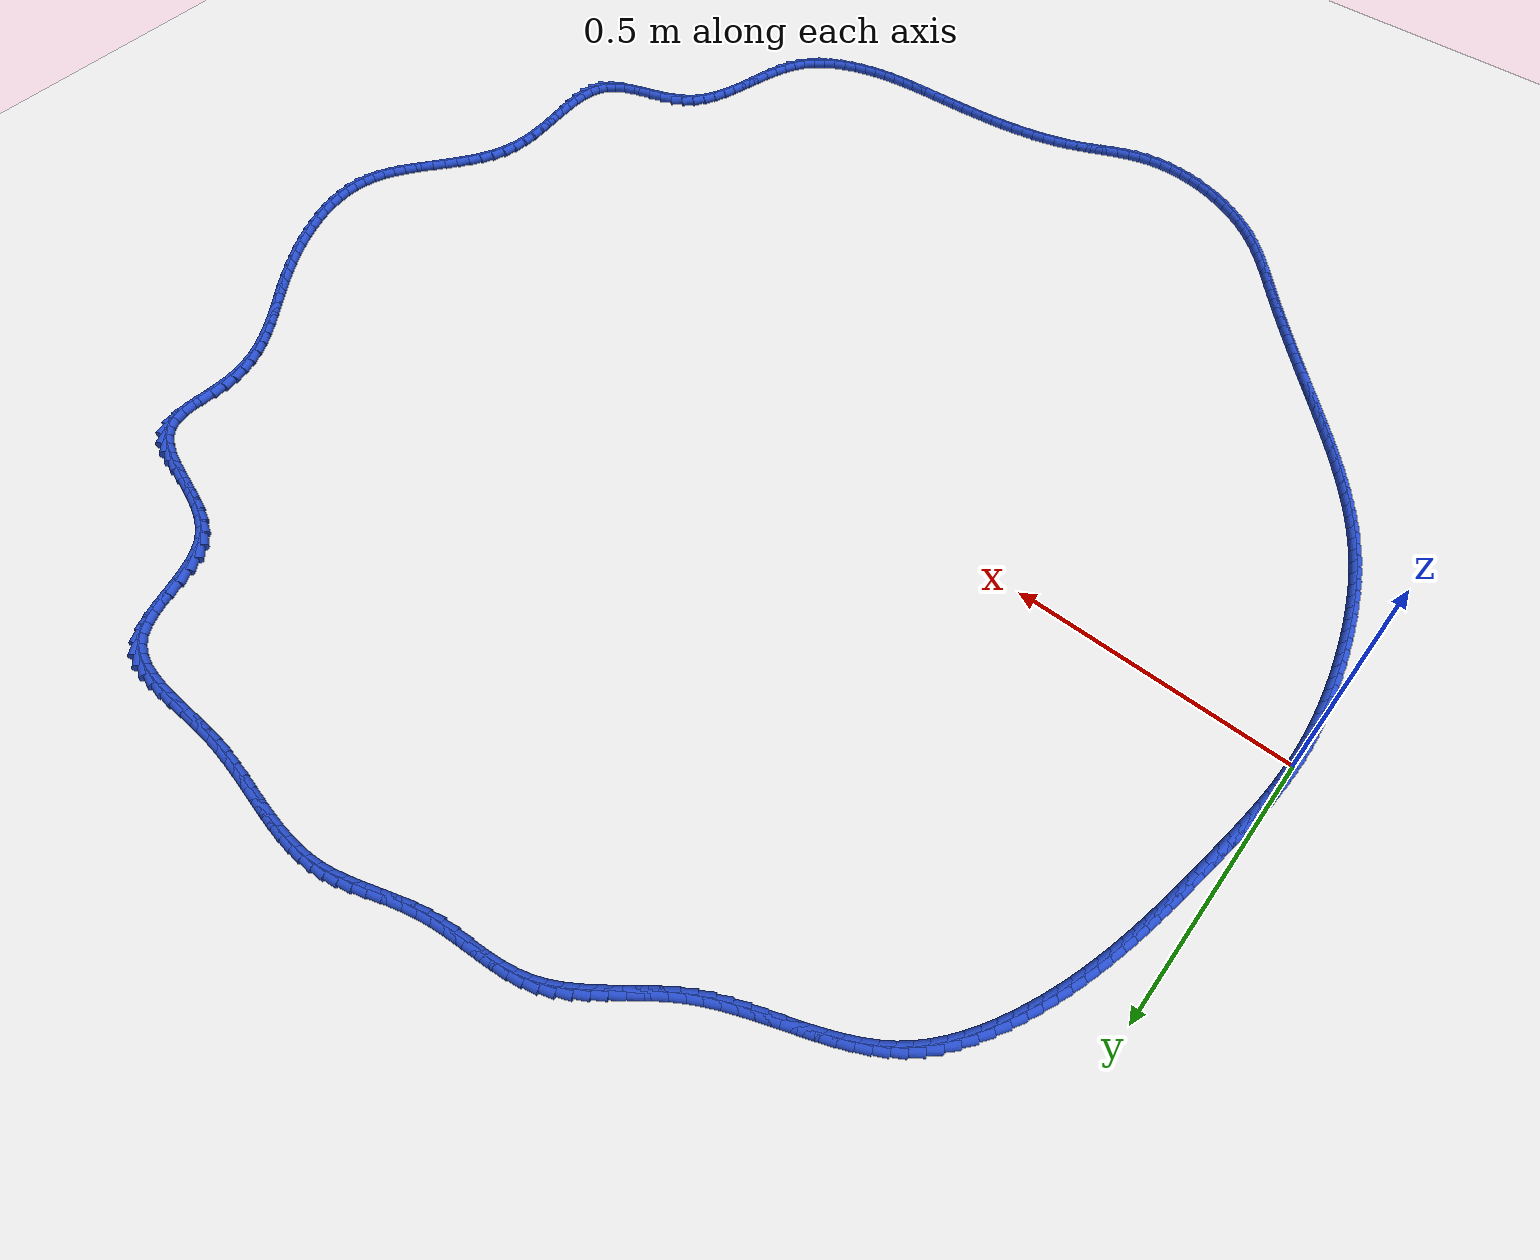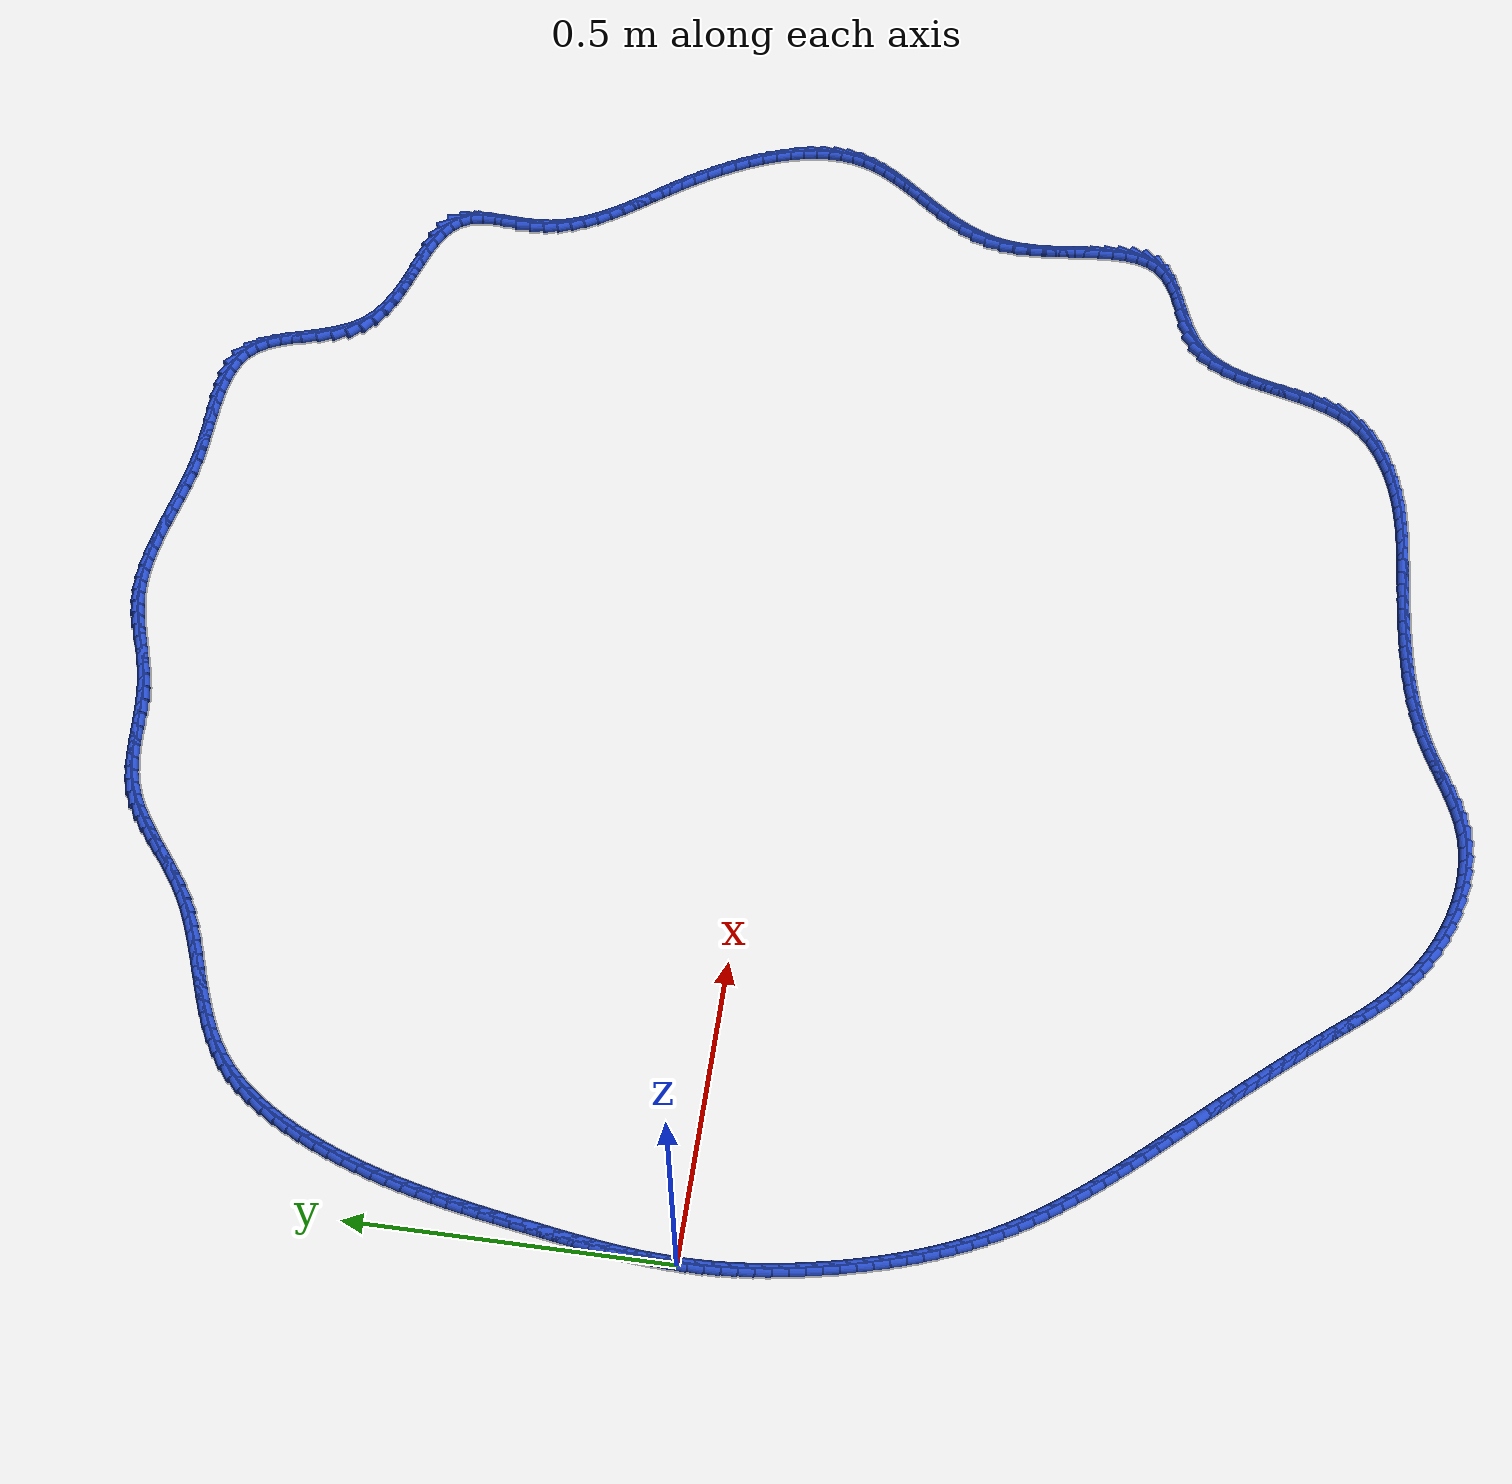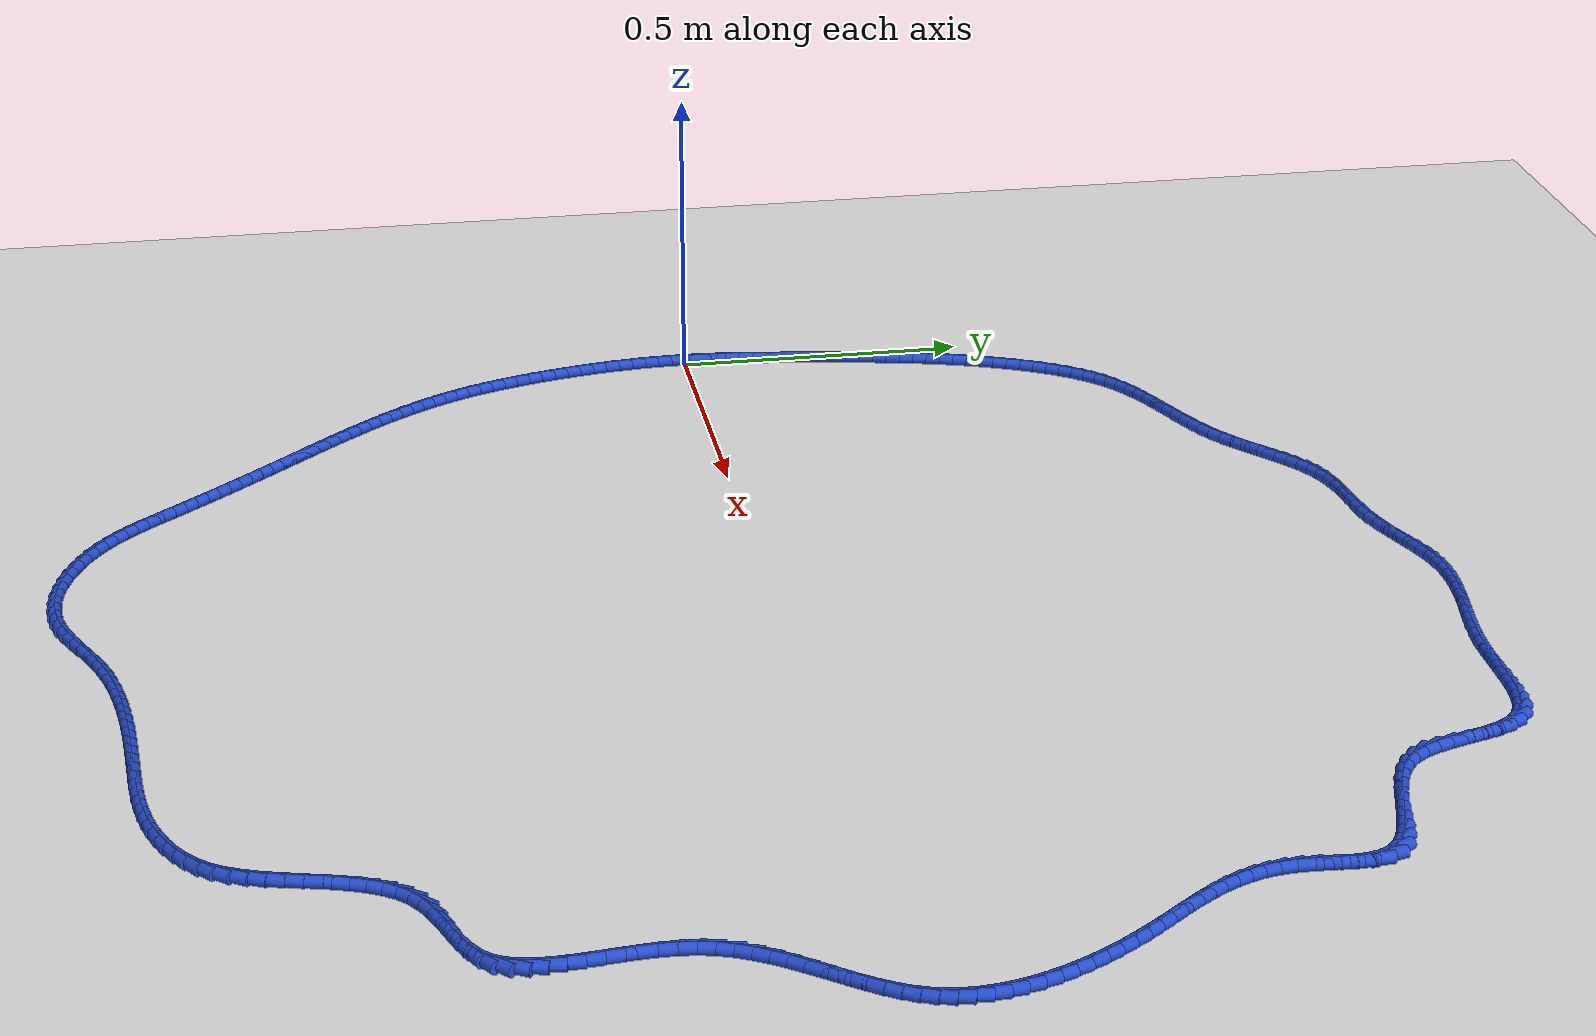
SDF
<sdf version="1.6">
 <world name="default">
  <light name="sun" type="directional">
   <pose>0 0 10 0 -0 0</pose>
   <diffuse>0.8 0.8 0.8 1</diffuse>
   <specular>0.2 0.2 0.2 1</specular>
   <attenuation>
    <range>1000</range>
    <constant>0.9</constant>
    <linear>0.01</linear>
    <quadratic>0.001</quadratic>
   </attenuation>
   <direction>-0.5 0.1 -0.9</direction>
  </light>
  <model name="ground_plane">
   <static>1</static>
   <link name="link">
    <collision name="collision">
     <geometry><plane><normal>0 0 1</normal><size>100 100</size></plane></geometry>
     <surface><friction><ode><mu>100</mu><mu2>50</mu2></ode></friction></surface>
    </collision>
    <visual name="visual">
     <cast_shadows>0</cast_shadows>
     <geometry><plane><normal>0 0 1</normal><size>100 100</size></plane></geometry>
     <material>
      <script><uri>file://media/materials/scripts/gazebo.material</uri><name>Gazebo/WhiteGlow</name></script>
     </material>
    </visual>
   </link>
  </model>
  <gravity>0 0 -9.8</gravity>
  <magnetic_field>6e-06 2.3e-05 -4.2e-05</magnetic_field>
  <atmosphere type="adiabatic"/>
  <physics name="default_physics" default="0" type="ode">
   <max_step_size>0.001</max_step_size>
   <real_time_factor>1</real_time_factor>
   <real_time_update_rate>1000</real_time_update_rate>
  </physics>
  <scene><ambient>0.4 0.4 0.4 1</ambient><background>0.7 0.7 0.7 1</background><shadows>1</shadows></scene>
  <spherical_coordinates>
   <surface_model>EARTH_WGS84</surface_model>
   <latitude_deg>0</latitude_deg>
   <longitude_deg>0</longitude_deg>
   <elevation>0</elevation>
   <heading_deg>0</heading_deg>
  </spherical_coordinates>
  <model name="line">
   <link name="link_0">
    <pose>4.336808689942018e-18 2.7755575615628914e-17 0.01 0 1.57 1.541240628306866</pose>
    <collision name="collision">
     <geometry><cylinder><radius>0.01</radius><length>0.08</length></cylinder></geometry>
    </collision>
    <visual name="visual">
     <material>
      <script><name>Gazebo/Blue</name><uri>file://media/materials/scripts/gazebo.material</uri></script>
     </material>
     <geometry><cylinder><radius>0.01</radius><length>0.08</length></cylinder></geometry>
    </visual>
   </link>
   <link name="link_1">
    <pose>0.0007195218230819837 0.024337516535822827 0.01 0 1.57 1.51308982490859</pose>
    <collision name="collision">
     <geometry><cylinder><radius>0.01</radius><length>0.08</length></cylinder></geometry>
    </collision>
    <visual name="visual">
     <material>
      <script><name>Gazebo/Blue</name><uri>file://media/materials/scripts/gazebo.material</uri></script>
     </material>
     <geometry><cylinder><radius>0.01</radius><length>0.08</length></cylinder></geometry>
    </visual>
   </link>
   <link name="link_2">
    <pose>0.0021244689404564727 0.048656912357331134 0.01 0 1.57 1.488278428723793</pose>
    <collision name="collision">
     <geometry><cylinder><radius>0.01</radius><length>0.08</length></cylinder></geometry>
    </collision>
    <visual name="visual">
     <material>
      <script><name>Gazebo/Blue</name><uri>file://media/materials/scripts/gazebo.material</uri></script>
     </material>
     <geometry><cylinder><radius>0.01</radius><length>0.08</length></cylinder></geometry>
    </visual>
   </link>
   <link name="link_3">
    <pose>0.004134289332251086 0.07295778050648408 0.01 0 1.57 1.4668095110842758</pose>
    <collision name="collision">
     <geometry><cylinder><radius>0.01</radius><length>0.08</length></cylinder></geometry>
    </collision>
    <visual name="visual">
     <material>
      <script><name>Gazebo/Blue</name><uri>file://media/materials/scripts/gazebo.material</uri></script>
     </material>
     <geometry><cylinder><radius>0.01</radius><length>0.08</length></cylinder></geometry>
    </visual>
   </link>
   <link name="link_4">
    <pose>0.006668430978593442 0.09723971402524081 0.01 0 1.57 1.4486704126826055</pose>
    <collision name="collision">
     <geometry><cylinder><radius>0.01</radius><length>0.08</length></cylinder></geometry>
    </collision>
    <visual name="visual">
     <material>
      <script><name>Gazebo/Blue</name><uri>file://media/materials/scripts/gazebo.material</uri></script>
     </material>
     <geometry><cylinder><radius>0.01</radius><length>0.08</length></cylinder></geometry>
    </visual>
   </link>
   <link name="link_5">
    <pose>0.009646341859611156 0.12150230595556051 0.01 0 1.57 1.4338399486752662</pose>
    <collision name="collision">
     <geometry><cylinder><radius>0.01</radius><length>0.08</length></cylinder></geometry>
    </collision>
    <visual name="visual">
     <material>
      <script><name>Gazebo/Blue</name><uri>file://media/materials/scripts/gazebo.material</uri></script>
     </material>
     <geometry><cylinder><radius>0.01</radius><length>0.08</length></cylinder></geometry>
    </visual>
   </link>
   <link name="link_6">
    <pose>0.012987469955431845 0.1457451493394023 0.01 0 1.57 1.4222944027254192</pose>
    <collision name="collision">
     <geometry><cylinder><radius>0.01</radius><length>0.08</length></cylinder></geometry>
    </collision>
    <visual name="visual">
     <material>
      <script><name>Gazebo/Blue</name><uri>file://media/materials/scripts/gazebo.material</uri></script>
     </material>
     <geometry><cylinder><radius>0.01</radius><length>0.08</length></cylinder></geometry>
    </visual>
   </link>
   <link name="link_7">
    <pose>0.016611263246183124 0.1699678372187253 0.01 0 1.57 1.4140123082852827</pose>
    <collision name="collision">
     <geometry><cylinder><radius>0.01</radius><length>0.08</length></cylinder></geometry>
    </collision>
    <visual name="visual">
     <material>
      <script><name>Gazebo/Blue</name><uri>file://media/materials/scripts/gazebo.material</uri></script>
     </material>
     <geometry><cylinder><radius>0.01</radius><length>0.08</length></cylinder></geometry>
    </visual>
   </link>
   <link name="link_8">
    <pose>0.02043716971199261 0.1941699626354887 0.01 0 1.57 1.4089780779462597</pose>
    <collision name="collision">
     <geometry><cylinder><radius>0.01</radius><length>0.08</length></cylinder></geometry>
    </collision>
    <visual name="visual">
     <material>
      <script><name>Gazebo/Blue</name><uri>file://media/materials/scripts/gazebo.material</uri></script>
     </material>
     <geometry><cylinder><radius>0.01</radius><length>0.08</length></cylinder></geometry>
    </visual>
   </link>
   <link name="link_9">
    <pose>0.02438463733298791 0.21835111863165158 0.01 0 1.57 1.4066696369151357</pose>
    <collision name="collision">
     <geometry><cylinder><radius>0.01</radius><length>0.08</length></cylinder></geometry>
    </collision>
    <visual name="visual">
     <material>
      <script><name>Gazebo/Blue</name><uri>file://media/materials/scripts/gazebo.material</uri></script>
     </material>
     <geometry><cylinder><radius>0.01</radius><length>0.08</length></cylinder></geometry>
    </visual>
   </link>
   <link name="link_10">
    <pose>0.028385738809748325 0.24250995680989818 0.01 0 1.57 1.4035984461523492</pose>
    <collision name="collision">
     <geometry><cylinder><radius>0.01</radius><length>0.08</length></cylinder></geometry>
    </collision>
    <visual name="visual">
     <material>
      <script><name>Gazebo/Blue</name><uri>file://media/materials/scripts/gazebo.material</uri></script>
     </material>
     <geometry><cylinder><radius>0.01</radius><length>0.08</length></cylinder></geometry>
    </visual>
   </link>
   <link name="link_11">
    <pose>0.03245804061749975 0.26663875340820453 0.01 0 1.57 1.3983135419564523</pose>
    <collision name="collision">
     <geometry><cylinder><radius>0.01</radius><length>0.08</length></cylinder></geometry>
    </collision>
    <visual name="visual">
     <material>
      <script><name>Gazebo/Blue</name><uri>file://media/materials/scripts/gazebo.material</uri></script>
     </material>
     <geometry><cylinder><radius>0.01</radius><length>0.08</length></cylinder></geometry>
    </visual>
   </link>
   <link name="link_12">
    <pose>0.036654571461395585 0.2907271402070984 0.01 0 1.57 1.390804693583547</pose>
    <collision name="collision">
     <geometry><cylinder><radius>0.01</radius><length>0.08</length></cylinder></geometry>
    </collision>
    <visual name="visual">
     <material>
      <script><name>Gazebo/Blue</name><uri>file://media/materials/scripts/gazebo.material</uri></script>
     </material>
     <geometry><cylinder><radius>0.01</radius><length>0.08</length></cylinder></geometry>
    </visual>
   </link>
   <link name="link_13">
    <pose>0.04102847448072235 0.3147647404536284 0.01 0 1.57 1.3810668655635585</pose>
    <collision name="collision">
     <geometry><cylinder><radius>0.01</radius><length>0.08</length></cylinder></geometry>
    </collision>
    <visual name="visual">
     <material>
      <script><name>Gazebo/Blue</name><uri>file://media/materials/scripts/gazebo.material</uri></script>
     </material>
     <geometry><cylinder><radius>0.01</radius><length>0.08</length></cylinder></geometry>
    </visual>
   </link>
   <link name="link_14">
    <pose>0.045632892814766596 0.33874117739484316 0.01 0 1.57 1.3690966697908817</pose>
    <collision name="collision">
     <geometry><cylinder><radius>0.01</radius><length>0.08</length></cylinder></geometry>
    </collision>
    <visual name="visual">
     <material>
      <script><name>Gazebo/Blue</name><uri>file://media/materials/scripts/gazebo.material</uri></script>
     </material>
     <geometry><cylinder><radius>0.01</radius><length>0.08</length></cylinder></geometry>
    </visual>
   </link>
   <link name="link_15">
    <pose>0.05052096960281487 0.3626460742777914 0.01 0 1.57 1.354893824899044</pose>
    <collision name="collision">
     <geometry><cylinder><radius>0.01</radius><length>0.08</length></cylinder></geometry>
    </collision>
    <visual name="visual">
     <material>
      <script><name>Gazebo/Blue</name><uri>file://media/materials/scripts/gazebo.material</uri></script>
     </material>
     <geometry><cylinder><radius>0.01</radius><length>0.08</length></cylinder></geometry>
    </visual>
   </link>
   <link name="link_16">
    <pose>0.0557458479841537 0.3864690543495217 0.01 0 1.57 1.3384629493589146</pose>
    <collision name="collision">
     <geometry><cylinder><radius>0.01</radius><length>0.08</length></cylinder></geometry>
    </collision>
    <visual name="visual">
     <material>
      <script><name>Gazebo/Blue</name><uri>file://media/materials/scripts/gazebo.material</uri></script>
     </material>
     <geometry><cylinder><radius>0.01</radius><length>0.08</length></cylinder></geometry>
    </visual>
   </link>
   <link name="link_17">
    <pose>0.061360671098069614 0.41019974085708294 0.01 0 1.57 1.3198156685415325</pose>
    <collision name="collision">
     <geometry><cylinder><radius>0.01</radius><length>0.08</length></cylinder></geometry>
    </collision>
    <visual name="visual">
     <material>
      <script><name>Gazebo/Blue</name><uri>file://media/materials/scripts/gazebo.material</uri></script>
     </material>
     <geometry><cylinder><radius>0.01</radius><length>0.08</length></cylinder></geometry>
    </visual>
   </link>
   <link name="link_18">
    <pose>0.06741858208384917 0.4338277570475237 0.01 0 1.57 1.2989729960919787</pose>
    <collision name="collision">
     <geometry><cylinder><radius>0.01</radius><length>0.08</length></cylinder></geometry>
    </collision>
    <visual name="visual">
     <material>
      <script><name>Gazebo/Blue</name><uri>file://media/materials/scripts/gazebo.material</uri></script>
     </material>
     <geometry><cylinder><radius>0.01</radius><length>0.08</length></cylinder></geometry>
    </visual>
   </link>
   <link name="link_19">
    <pose>0.0739727240807789 0.45734272616789257 0.01 0 1.57 1.2759679231702117</pose>
    <collision name="collision">
     <geometry><cylinder><radius>0.01</radius><length>0.08</length></cylinder></geometry>
    </collision>
    <visual name="visual">
     <material>
      <script><name>Gazebo/Blue</name><uri>file://media/materials/scripts/gazebo.material</uri></script>
     </material>
     <geometry><cylinder><radius>0.01</radius><length>0.08</length></cylinder></geometry>
    </visual>
   </link>
   <link name="link_20">
    <pose>0.08107624022814534 0.4807342714652384 0.01 0 1.57 1.2508481159569462</pose>
    <collision name="collision">
     <geometry><cylinder><radius>0.01</radius><length>0.08</length></cylinder></geometry>
    </collision>
    <visual name="visual">
     <material>
      <script><name>Gazebo/Blue</name><uri>file://media/materials/scripts/gazebo.material</uri></script>
     </material>
     <geometry><cylinder><radius>0.01</radius><length>0.08</length></cylinder></geometry>
    </visual>
   </link>
   <link name="link_21">
    <pose>0.08878227366523503 0.5039920161866096 0.01 0 1.57 1.2236785842281588</pose>
    <collision name="collision">
     <geometry><cylinder><radius>0.01</radius><length>0.08</length></cylinder></geometry>
    </collision>
    <visual name="visual">
     <material>
      <script><name>Gazebo/Blue</name><uri>file://media/materials/scripts/gazebo.material</uri></script>
     </material>
     <geometry><cylinder><radius>0.01</radius><length>0.08</length></cylinder></geometry>
    </visual>
   </link>
   <link name="link_22">
    <pose>0.0971439675313345 0.5271055835790551 0.01 0 1.57 1.1945441455069041</pose>
    <collision name="collision">
     <geometry><cylinder><radius>0.01</radius><length>0.08</length></cylinder></geometry>
    </collision>
    <visual name="visual">
     <material>
      <script><name>Gazebo/Blue</name><uri>file://media/materials/scripts/gazebo.material</uri></script>
     </material>
     <geometry><cylinder><radius>0.01</radius><length>0.08</length></cylinder></geometry>
    </visual>
   </link>
   <link name="link_23">
    <pose>0.10621446496573032 0.5500645968896236 0.01 0 1.57 1.1635514760319494</pose>
    <collision name="collision">
     <geometry><cylinder><radius>0.01</radius><length>0.08</length></cylinder></geometry>
    </collision>
    <visual name="visual">
     <material>
      <script><name>Gazebo/Blue</name><uri>file://media/materials/scripts/gazebo.material</uri></script>
     </material>
     <geometry><cylinder><radius>0.01</radius><length>0.08</length></cylinder></geometry>
    </visual>
   </link>
   <link name="link_24">
    <pose>0.11604690910770901 0.5728586793653636 0.01 0 1.57 1.1304806581128175</pose>
    <collision name="collision">
     <geometry><cylinder><radius>0.01</radius><length>0.08</length></cylinder></geometry>
    </collision>
    <visual name="visual">
     <material>
      <script><name>Gazebo/Blue</name><uri>file://media/materials/scripts/gazebo.material</uri></script>
     </material>
     <geometry><cylinder><radius>0.01</radius><length>0.08</length></cylinder></geometry>
    </visual>
   </link>
   <link name="link_25">
    <pose>0.1266951397989091 0.5954584123743284 0.01 0 1.57 1.0928553787636517</pose>
    <collision name="collision">
     <geometry><cylinder><radius>0.01</radius><length>0.08</length></cylinder></geometry>
    </collision>
    <visual name="visual">
     <material>
      <script><name>Gazebo/Blue</name><uri>file://media/materials/scripts/gazebo.material</uri></script>
     </material>
     <geometry><cylinder><radius>0.01</radius><length>0.08</length></cylinder></geometry>
    </visual>
   </link>
   <link name="link_26">
    <pose>0.13821780072810833 0.6177030812215369 0.01 0 1.57 1.0491190272679338</pose>
    <collision name="collision">
     <geometry><cylinder><radius>0.01</radius><length>0.08</length></cylinder></geometry>
    </collision>
    <visual name="visual">
     <material>
      <script><name>Gazebo/Blue</name><uri>file://media/materials/scripts/gazebo.material</uri></script>
     </material>
     <geometry><cylinder><radius>0.01</radius><length>0.08</length></cylinder></geometry>
    </visual>
   </link>
   <link name="link_27">
    <pose>0.150675560646322 0.6393766233436146 0.01 0 1.57 0.9985542025627883</pose>
    <collision name="collision">
     <geometry><cylinder><radius>0.01</radius><length>0.08</length></cylinder></geometry>
    </collision>
    <visual name="visual">
     <material>
      <script><name>Gazebo/Blue</name><uri>file://media/materials/scripts/gazebo.material</uri></script>
     </material>
     <geometry><cylinder><radius>0.01</radius><length>0.08</length></cylinder></geometry>
    </visual>
   </link>
   <link name="link_28">
    <pose>0.16412909541280596 0.6602627818987412 0.01 0 1.57 0.94035812001997</pose>
    <collision name="collision">
     <geometry><cylinder><radius>0.01</radius><length>0.08</length></cylinder></geometry>
    </collision>
    <visual name="visual">
     <material>
      <script><name>Gazebo/Blue</name><uri>file://media/materials/scripts/gazebo.material</uri></script>
     </material>
     <geometry><cylinder><radius>0.01</radius><length>0.08</length></cylinder></geometry>
    </visual>
   </link>
   <link name="link_29">
    <pose>0.17863908088681588 0.6801453000450963 0.01 0 1.57 0.8736932939423195</pose>
    <collision name="collision">
     <geometry><cylinder><radius>0.01</radius><length>0.08</length></cylinder></geometry>
    </collision>
    <visual name="visual">
     <material>
      <script><name>Gazebo/Blue</name><uri>file://media/materials/scripts/gazebo.material</uri></script>
     </material>
     <geometry><cylinder><radius>0.01</radius><length>0.08</length></cylinder></geometry>
    </visual>
   </link>
   <link name="link_30">
    <pose>0.1942661929276074 0.6988079209408593 0.01 0 1.57 0.797784694931443</pose>
    <collision name="collision">
     <geometry><cylinder><radius>0.01</radius><length>0.08</length></cylinder></geometry>
    </collision>
    <visual name="visual">
     <material>
      <script><name>Gazebo/Blue</name><uri>file://media/materials/scripts/gazebo.material</uri></script>
     </material>
     <geometry><cylinder><radius>0.01</radius><length>0.08</length></cylinder></geometry>
    </visual>
   </link>
   <link name="link_31">
    <pose>0.21107110739443624 0.7160343877442097 0.01 0 1.57 0.7121474746974692</pose>
    <collision name="collision">
     <geometry><cylinder><radius>0.01</radius><length>0.08</length></cylinder></geometry>
    </collision>
    <visual name="visual">
     <material>
      <script><name>Gazebo/Blue</name><uri>file://media/materials/scripts/gazebo.material</uri></script>
     </material>
     <geometry><cylinder><radius>0.01</radius><length>0.08</length></cylinder></geometry>
    </visual>
   </link>
   <link name="link_32">
    <pose>0.22911373461113171 0.7316100390092171 0.01 0 1.57 0.6239749532948126</pose>
    <collision name="collision">
     <geometry><cylinder><radius>0.01</radius><length>0.08</length></cylinder></geometry>
    </collision>
    <visual name="visual">
     <material>
      <script><name>Gazebo/Blue</name><uri>file://media/materials/scripts/gazebo.material</uri></script>
     </material>
     <geometry><cylinder><radius>0.01</radius><length>0.08</length></cylinder></geometry>
    </visual>
   </link>
   <link name="link_33">
    <pose>0.24837788039571584 0.7454788170744854 0.01 0 1.57 0.5475864809184215</pose>
    <collision name="collision">
     <geometry><cylinder><radius>0.01</radius><length>0.08</length></cylinder></geometry>
    </collision>
    <visual name="visual">
     <material>
      <script><name>Gazebo/Blue</name><uri>file://media/materials/scripts/gazebo.material</uri></script>
     </material>
     <geometry><cylinder><radius>0.01</radius><length>0.08</length></cylinder></geometry>
    </visual>
   </link>
   <link name="link_34">
    <pose>0.26870769072387285 0.7578757190500409 0.01 0 1.57 0.485228002487949</pose>
    <collision name="collision">
     <geometry><cylinder><radius>0.01</radius><length>0.08</length></cylinder></geometry>
    </collision>
    <visual name="visual">
     <material>
      <script><name>Gazebo/Blue</name><uri>file://media/materials/scripts/gazebo.material</uri></script>
     </material>
     <geometry><cylinder><radius>0.01</radius><length>0.08</length></cylinder></geometry>
    </visual>
   </link>
   <link name="link_35">
    <pose>0.2899323469080472 0.7690669287962737 0.01 0 1.57 0.4369631693404891</pose>
    <collision name="collision">
     <geometry><cylinder><radius>0.01</radius><length>0.08</length></cylinder></geometry>
    </collision>
    <visual name="visual">
     <material>
      <script><name>Gazebo/Blue</name><uri>file://media/materials/scripts/gazebo.material</uri></script>
     </material>
     <geometry><cylinder><radius>0.01</radius><length>0.08</length></cylinder></geometry>
    </visual>
   </link>
   <link name="link_36">
    <pose>0.31188103026068315 0.7793186301735731 0.01 0 1.57 0.4024378775957611</pose>
    <collision name="collision">
     <geometry><cylinder><radius>0.01</radius><length>0.08</length></cylinder></geometry>
    </collision>
    <visual name="visual">
     <material>
      <script><name>Gazebo/Blue</name><uri>file://media/materials/scripts/gazebo.material</uri></script>
     </material>
     <geometry><cylinder><radius>0.01</radius><length>0.08</length></cylinder></geometry>
    </visual>
   </link>
   <link name="link_37">
    <pose>0.33438292209422577 0.7888970070423291 0.01 0 1.57 0.38116632947380613</pose>
    <collision name="collision">
     <geometry><cylinder><radius>0.01</radius><length>0.08</length></cylinder></geometry>
    </collision>
    <visual name="visual">
     <material>
      <script><name>Gazebo/Blue</name><uri>file://media/materials/scripts/gazebo.material</uri></script>
     </material>
     <geometry><cylinder><radius>0.01</radius><length>0.08</length></cylinder></geometry>
    </visual>
   </link>
   <link name="link_38">
    <pose>0.3572672037211187 0.7980682432629304 0.01 0 1.57 0.372716286954041</pose>
    <collision name="collision">
     <geometry><cylinder><radius>0.01</radius><length>0.08</length></cylinder></geometry>
    </collision>
    <visual name="visual">
     <material>
      <script><name>Gazebo/Blue</name><uri>file://media/materials/scripts/gazebo.material</uri></script>
     </material>
     <geometry><cylinder><radius>0.01</radius><length>0.08</length></cylinder></geometry>
    </visual>
   </link>
   <link name="link_39">
    <pose>0.3803630564538072 0.8070985226957674 0.01 0 1.57 0.3768071415485865</pose>
    <collision name="collision">
     <geometry><cylinder><radius>0.01</radius><length>0.08</length></cylinder></geometry>
    </collision>
    <visual name="visual">
     <material>
      <script><name>Gazebo/Blue</name><uri>file://media/materials/scripts/gazebo.material</uri></script>
     </material>
     <geometry><cylinder><radius>0.01</radius><length>0.08</length></cylinder></geometry>
    </visual>
   </link>
   <link name="link_40">
    <pose>0.40349966160473516 0.8162540292012294 0.01 0 1.57 0.3933406382831516</pose>
    <collision name="collision">
     <geometry><cylinder><radius>0.01</radius><length>0.08</length></cylinder></geometry>
    </collision>
    <visual name="visual">
     <material>
      <script><name>Gazebo/Blue</name><uri>file://media/materials/scripts/gazebo.material</uri></script>
     </material>
     <geometry><cylinder><radius>0.01</radius><length>0.08</length></cylinder></geometry>
    </visual>
   </link>
   <link name="link_41">
    <pose>0.42650620048634746 0.825800946639706 0.01 0 1.57 0.422376521784005</pose>
    <collision name="collision">
     <geometry><cylinder><radius>0.01</radius><length>0.08</length></cylinder></geometry>
    </collision>
    <visual name="visual">
     <material>
      <script><name>Gazebo/Blue</name><uri>file://media/materials/scripts/gazebo.material</uri></script>
     </material>
     <geometry><cylinder><radius>0.01</radius><length>0.08</length></cylinder></geometry>
    </visual>
   </link>
   <link name="link_42">
    <pose>0.44921185441108835 0.8360054588715871 0.01 0 1.57 0.4640546780678825</pose>
    <collision name="collision">
     <geometry><cylinder><radius>0.01</radius><length>0.08</length></cylinder></geometry>
    </collision>
    <visual name="visual">
     <material>
      <script><name>Gazebo/Blue</name><uri>file://media/materials/scripts/gazebo.material</uri></script>
     </material>
     <geometry><cylinder><radius>0.01</radius><length>0.08</length></cylinder></geometry>
    </visual>
   </link>
   <link name="link_43">
    <pose>0.4714458046914022 0.8471337497572615 0.01 0 1.57 0.5184578456901792</pose>
    <collision name="collision">
     <geometry><cylinder><radius>0.01</radius><length>0.08</length></cylinder></geometry>
    </collision>
    <visual name="visual">
     <material>
      <script><name>Gazebo/Blue</name><uri>file://media/materials/scripts/gazebo.material</uri></script>
     </material>
     <geometry><cylinder><radius>0.01</radius><length>0.08</length></cylinder></geometry>
    </visual>
   </link>
   <link name="link_44">
    <pose>0.49303723263973376 0.8594520031571193 0.01 0 1.57 0.5814403331454062</pose>
    <collision name="collision">
     <geometry><cylinder><radius>0.01</radius><length>0.08</length></cylinder></geometry>
    </collision>
    <visual name="visual">
     <material>
      <script><name>Gazebo/Blue</name><uri>file://media/materials/scripts/gazebo.material</uri></script>
     </material>
     <geometry><cylinder><radius>0.01</radius><length>0.08</length></cylinder></geometry>
    </visual>
   </link>
   <link name="link_45">
    <pose>0.5138615754891978 0.8731383648626725 0.01 0 1.57 0.6314804484326801</pose>
    <collision name="collision">
     <geometry><cylinder><radius>0.01</radius><length>0.08</length></cylinder></geometry>
    </collision>
    <visual name="visual">
     <material>
      <script><name>Gazebo/Blue</name><uri>file://media/materials/scripts/gazebo.material</uri></script>
     </material>
     <geometry><cylinder><radius>0.01</radius><length>0.08</length></cylinder></geometry>
    </visual>
   </link>
   <link name="link_46">
    <pose>0.5340425556417864 0.8878984239314586 0.01 0 1.57 0.6618253283691095</pose>
    <collision name="collision">
     <geometry><cylinder><radius>0.01</radius><length>0.08</length></cylinder></geometry>
    </collision>
    <visual name="visual">
     <material>
      <script><name>Gazebo/Blue</name><uri>file://media/materials/scripts/gazebo.material</uri></script>
     </material>
     <geometry><cylinder><radius>0.01</radius><length>0.08</length></cylinder></geometry>
    </visual>
   </link>
   <link name="link_47">
    <pose>0.5537868447146543 0.9032798936591221 0.01 0 1.57 0.672832629722732</pose>
    <collision name="collision">
     <geometry><cylinder><radius>0.01</radius><length>0.08</length></cylinder></geometry>
    </collision>
    <visual name="visual">
     <material>
      <script><name>Gazebo/Blue</name><uri>file://media/materials/scripts/gazebo.material</uri></script>
     </material>
     <geometry><cylinder><radius>0.01</radius><length>0.08</length></cylinder></geometry>
    </visual>
   </link>
   <link name="link_48">
    <pose>0.573301172642326 0.9188303763469021 0.01 0 1.57 0.6644658982052908</pose>
    <collision name="collision">
     <geometry><cylinder><radius>0.01</radius><length>0.08</length></cylinder></geometry>
    </collision>
    <visual name="visual">
     <material>
      <script><name>Gazebo/Blue</name><uri>file://media/materials/scripts/gazebo.material</uri></script>
     </material>
     <geometry><cylinder><radius>0.01</radius><length>0.08</length></cylinder></geometry>
    </visual>
   </link>
   <link name="link_49">
    <pose>0.5927922693593244 0.934097474296035 0.01 0 1.57 0.6361538931488236</pose>
    <collision name="collision">
     <geometry><cylinder><radius>0.01</radius><length>0.08</length></cylinder></geometry>
    </collision>
    <visual name="visual">
     <material>
      <script><name>Gazebo/Blue</name><uri>file://media/materials/scripts/gazebo.material</uri></script>
     </material>
     <geometry><cylinder><radius>0.01</radius><length>0.08</length></cylinder></geometry>
    </visual>
   </link>
   <link name="link_50">
    <pose>0.6124668648001732 0.948628789807759 0.01 0 1.57 0.5868488147586071</pose>
    <collision name="collision">
     <geometry><cylinder><radius>0.01</radius><length>0.08</length></cylinder></geometry>
    </collision>
    <visual name="visual">
     <material>
      <script><name>Gazebo/Blue</name><uri>file://media/materials/scripts/gazebo.material</uri></script>
     </material>
     <geometry><cylinder><radius>0.01</radius><length>0.08</length></cylinder></geometry>
    </visual>
   </link>
   <link name="link_51">
    <pose>0.6325316888993958 0.9619719251833114 0.01 0 1.57 0.5153370140667631</pose>
    <collision name="collision">
     <geometry><cylinder><radius>0.01</radius><length>0.08</length></cylinder></geometry>
    </collision>
    <visual name="visual">
     <material>
      <script><name>Gazebo/Blue</name><uri>file://media/materials/scripts/gazebo.material</uri></script>
     </material>
     <geometry><cylinder><radius>0.01</radius><length>0.08</length></cylinder></geometry>
    </visual>
   </link>
   <link name="link_52">
    <pose>0.6531934715915163 0.9736744827239309 0.01 0 1.57 0.42091982767863056</pose>
    <collision name="collision">
     <geometry><cylinder><radius>0.01</radius><length>0.08</length></cylinder></geometry>
    </collision>
    <visual name="visual">
     <material>
      <script><name>Gazebo/Blue</name><uri>file://media/materials/scripts/gazebo.material</uri></script>
     </material>
     <geometry><cylinder><radius>0.01</radius><length>0.08</length></cylinder></geometry>
    </visual>
   </link>
   <link name="link_53">
    <pose>0.6746589428110578 0.983284064730854 0.01 0 1.57 0.3113556151825807</pose>
    <collision name="collision">
     <geometry><cylinder><radius>0.01</radius><length>0.08</length></cylinder></geometry>
    </collision>
    <visual name="visual">
     <material>
      <script><name>Gazebo/Blue</name><uri>file://media/materials/scripts/gazebo.material</uri></script>
     </material>
     <geometry><cylinder><radius>0.01</radius><length>0.08</length></cylinder></geometry>
    </visual>
   </link>
   <link name="link_54">
    <pose>0.6970769392252876 0.9904986886721905 0.01 0 1.57 0.21963390347332945</pose>
    <collision name="collision">
     <geometry><cylinder><radius>0.01</radius><length>0.08</length></cylinder></geometry>
    </collision>
    <visual name="visual">
     <material>
      <script><name>Gazebo/Blue</name><uri>file://media/materials/scripts/gazebo.material</uri></script>
     </material>
     <geometry><cylinder><radius>0.01</radius><length>0.08</length></cylinder></geometry>
    </visual>
   </link>
   <link name="link_55">
    <pose>0.7203366155492823 0.9956910636688654 0.01 0 1.57 0.15478383223184994</pose>
    <collision name="collision">
     <geometry><cylinder><radius>0.01</radius><length>0.08</length></cylinder></geometry>
    </collision>
    <visual name="visual">
     <material>
      <script><name>Gazebo/Blue</name><uri>file://media/materials/scripts/gazebo.material</uri></script>
     </material>
     <geometry><cylinder><radius>0.01</radius><length>0.08</length></cylinder></geometry>
    </visual>
   </link>
   <link name="link_56">
    <pose>0.7442543462269555 0.9994229926198983 0.01 0 1.57 0.11563778552036559</pose>
    <collision name="collision">
     <geometry><cylinder><radius>0.01</radius><length>0.08</length></cylinder></geometry>
    </collision>
    <visual name="visual">
     <material>
      <script><name>Gazebo/Blue</name><uri>file://media/materials/scripts/gazebo.material</uri></script>
     </material>
     <geometry><cylinder><radius>0.01</radius><length>0.08</length></cylinder></geometry>
    </visual>
   </link>
   <link name="link_57">
    <pose>0.7686465020883363 1.0022562878137133 0.01 0 1.57 0.1007988405325589</pose>
    <collision name="collision">
     <geometry><cylinder><radius>0.01</radius><length>0.08</length></cylinder></geometry>
    </collision>
    <visual name="visual">
     <material>
      <script><name>Gazebo/Blue</name><uri>file://media/materials/scripts/gazebo.material</uri></script>
     </material>
     <geometry><cylinder><radius>0.01</radius><length>0.08</length></cylinder></geometry>
    </visual>
   </link>
   <link name="link_58">
    <pose>0.7933294539634524 1.0047527615387333 0.01 0 1.57 0.1093423634695897</pose>
    <collision name="collision">
     <geometry><cylinder><radius>0.01</radius><length>0.08</length></cylinder></geometry>
    </collision>
    <visual name="visual">
     <material>
      <script><name>Gazebo/Blue</name><uri>file://media/materials/scripts/gazebo.material</uri></script>
     </material>
     <geometry><cylinder><radius>0.01</radius><length>0.08</length></cylinder></geometry>
    </visual>
   </link>
   <link name="link_59">
    <pose>0.8181195726823325 1.0074742260833824 0.01 0 1.57 0.14101445191665365</pose>
    <collision name="collision">
     <geometry><cylinder><radius>0.01</radius><length>0.08</length></cylinder></geometry>
    </collision>
    <visual name="visual">
     <material>
      <script><name>Gazebo/Blue</name><uri>file://media/materials/scripts/gazebo.material</uri></script>
     </material>
     <geometry><cylinder><radius>0.01</radius><length>0.08</length></cylinder></geometry>
    </visual>
   </link>
   <link name="link_60">
    <pose>0.8428332290750047 1.0109824937360838 0.01 0 1.57 0.19597438036675618</pose>
    <collision name="collision">
     <geometry><cylinder><radius>0.01</radius><length>0.08</length></cylinder></geometry>
    </collision>
    <visual name="visual">
     <material>
      <script><name>Gazebo/Blue</name><uri>file://media/materials/scripts/gazebo.material</uri></script>
     </material>
     <geometry><cylinder><radius>0.01</radius><length>0.08</length></cylinder></geometry>
    </visual>
   </link>
   <link name="link_61">
    <pose>0.8672872637894665 1.015837167209766 0.01 0 1.57 0.2606775421399852</pose>
    <collision name="collision">
     <geometry><cylinder><radius>0.01</radius><length>0.08</length></cylinder></geometry>
    </collision>
    <visual name="visual">
     <material>
      <script><name>Gazebo/Blue</name><uri>file://media/materials/scripts/gazebo.material</uri></script>
     </material>
     <geometry><cylinder><radius>0.01</radius><length>0.08</length></cylinder></geometry>
    </visual>
   </link>
   <link name="link_62">
    <pose>0.8913700995711199 1.0222611953243048 0.01 0 1.57 0.3067265759131802</pose>
    <collision name="collision">
     <geometry><cylinder><radius>0.01</radius><length>0.08</length></cylinder></geometry>
    </collision>
    <visual name="visual">
     <material>
      <script><name>Gazebo/Blue</name><uri>file://media/materials/scripts/gazebo.material</uri></script>
     </material>
     <geometry><cylinder><radius>0.01</radius><length>0.08</length></cylinder></geometry>
    </visual>
   </link>
   <link name="link_63">
    <pose>0.9151179098923152 1.0297826484420853 0.01 0 1.57 0.3308754575620428</pose>
    <collision name="collision">
     <geometry><cylinder><radius>0.01</radius><length>0.08</length></cylinder></geometry>
    </collision>
    <visual name="visual">
     <material>
      <script><name>Gazebo/Blue</name><uri>file://media/materials/scripts/gazebo.material</uri></script>
     </material>
     <geometry><cylinder><radius>0.01</radius><length>0.08</length></cylinder></geometry>
    </visual>
   </link>
   <link name="link_64">
    <pose>0.9385851288622677 1.0378437163113008 0.01 0 1.57 0.33316320500439944</pose>
    <collision name="collision">
     <geometry><cylinder><radius>0.01</radius><length>0.08</length></cylinder></geometry>
    </collision>
    <visual name="visual">
     <material>
      <script><name>Gazebo/Blue</name><uri>file://media/materials/scripts/gazebo.material</uri></script>
     </material>
     <geometry><cylinder><radius>0.01</radius><length>0.08</length></cylinder></geometry>
    </visual>
   </link>
   <link name="link_65">
    <pose>0.9618261905901928 1.0458865886801443 0.01 0 1.57 0.313029030890931</pose>
    <collision name="collision">
     <geometry><cylinder><radius>0.01</radius><length>0.08</length></cylinder></geometry>
    </collision>
    <visual name="visual">
     <material>
      <script><name>Gazebo/Blue</name><uri>file://media/materials/scripts/gazebo.material</uri></script>
     </material>
     <geometry><cylinder><radius>0.01</radius><length>0.08</length></cylinder></geometry>
    </visual>
   </link>
   <link name="link_66">
    <pose>0.9848955291853061 1.0533534552968096 0.01 0 1.57 0.26922622897435544</pose>
    <collision name="collision">
     <geometry><cylinder><radius>0.01</radius><length>0.08</length></cylinder></geometry>
    </collision>
    <visual name="visual">
     <material>
      <script><name>Gazebo/Blue</name><uri>file://media/materials/scripts/gazebo.material</uri></script>
     </material>
     <geometry><cylinder><radius>0.01</radius><length>0.08</length></cylinder></geometry>
    </visual>
   </link>
   <link name="link_67">
    <pose>1.0078475787568224 1.0596865059094895 0.01 0 1.57 0.2001209866895441</pose>
    <collision name="collision">
     <geometry><cylinder><radius>0.01</radius><length>0.08</length></cylinder></geometry>
    </collision>
    <visual name="visual">
     <material>
      <script><name>Gazebo/Blue</name><uri>file://media/materials/scripts/gazebo.material</uri></script>
     </material>
     <geometry><cylinder><radius>0.01</radius><length>0.08</length></cylinder></geometry>
    </visual>
   </link>
   <link name="link_68">
    <pose>1.0307367813749222 1.0643292601383858 0.01 0 1.57 0.11470862202589946</pose>
    <collision name="collision">
     <geometry><cylinder><radius>0.01</radius><length>0.08</length></cylinder></geometry>
    </collision>
    <visual name="visual">
     <material>
      <script><name>Gazebo/Blue</name><uri>file://media/materials/scripts/gazebo.material</uri></script>
     </material>
     <geometry><cylinder><radius>0.01</radius><length>0.08</length></cylinder></geometry>
    </visual>
   </link>
   <link name="link_69">
    <pose>1.053619018122045 1.066965623289 0.01 0 1.57 0.03622314952101029</pose>
    <collision name="collision">
     <geometry><cylinder><radius>0.01</radius><length>0.08</length></cylinder></geometry>
    </collision>
    <visual name="visual">
     <material>
      <script><name>Gazebo/Blue</name><uri>file://media/materials/scripts/gazebo.material</uri></script>
     </material>
     <geometry><cylinder><radius>0.01</radius><length>0.08</length></cylinder></geometry>
    </visual>
   </link>
   <link name="link_70">
    <pose>1.0765532663972324 1.0677967375314794 0.01 0 1.57 -0.030619816489129974</pose>
    <collision name="collision">
     <geometry><cylinder><radius>0.01</radius><length>0.08</length></cylinder></geometry>
    </collision>
    <visual name="visual">
     <material>
      <script><name>Gazebo/Blue</name><uri>file://media/materials/scripts/gazebo.material</uri></script>
     </material>
     <geometry><cylinder><radius>0.01</radius><length>0.08</length></cylinder></geometry>
    </visual>
   </link>
   <link name="link_71">
    <pose>1.0995989053894601 1.0670908636780791 0.01 0 1.57 -0.08484776397649875</pose>
    <collision name="collision">
     <geometry><cylinder><radius>0.01</radius><length>0.08</length></cylinder></geometry>
    </collision>
    <visual name="visual">
     <material>
      <script><name>Gazebo/Blue</name><uri>file://media/materials/scripts/gazebo.material</uri></script>
     </material>
     <geometry><cylinder><radius>0.01</radius><length>0.08</length></cylinder></geometry>
    </visual>
   </link>
   <link name="link_72">
    <pose>1.1228153142877038 1.0651162625410544 0.01 0 1.57 -0.1262127067082713</pose>
    <collision name="collision">
     <geometry><cylinder><radius>0.01</radius><length>0.08</length></cylinder></geometry>
    </collision>
    <visual name="visual">
     <material>
      <script><name>Gazebo/Blue</name><uri>file://media/materials/scripts/gazebo.material</uri></script>
     </material>
     <geometry><cylinder><radius>0.01</radius><length>0.08</length></cylinder></geometry>
    </visual>
   </link>
   <link name="link_73">
    <pose>1.1462618722809406 1.0621411949326593 0.01 0 1.57 -0.154935454982123</pose>
    <collision name="collision">
     <geometry><cylinder><radius>0.01</radius><length>0.08</length></cylinder></geometry>
    </collision>
    <visual name="visual">
     <material>
      <script><name>Gazebo/Blue</name><uri>file://media/materials/scripts/gazebo.material</uri></script>
     </material>
     <geometry><cylinder><radius>0.01</radius><length>0.08</length></cylinder></geometry>
    </visual>
   </link>
   <link name="link_74">
    <pose>1.1699979585581455 1.0584339216651493 0.01 0 1.57 -0.17148641508600737</pose>
    <collision name="collision">
     <geometry><cylinder><radius>0.01</radius><length>0.08</length></cylinder></geometry>
    </collision>
    <visual name="visual">
     <material>
      <script><name>Gazebo/Blue</name><uri>file://media/materials/scripts/gazebo.material</uri></script>
     </material>
     <geometry><cylinder><radius>0.01</radius><length>0.08</length></cylinder></geometry>
    </visual>
   </link>
   <link name="link_75">
    <pose>1.1940829523082948 1.0542627035507788 0.01 0 1.57 -0.1764359204703832</pose>
    <collision name="collision">
     <geometry><cylinder><radius>0.01</radius><length>0.08</length></cylinder></geometry>
    </collision>
    <visual name="visual">
     <material>
      <script><name>Gazebo/Blue</name><uri>file://media/materials/scripts/gazebo.material</uri></script>
     </material>
     <geometry><cylinder><radius>0.01</radius><length>0.08</length></cylinder></geometry>
    </visual>
   </link>
   <link name="link_76">
    <pose>1.218576232720365 1.049895801401803 0.01 0 1.57 -0.17037390539857214</pose>
    <collision name="collision">
     <geometry><cylinder><radius>0.01</radius><length>0.08</length></cylinder></geometry>
    </collision>
    <visual name="visual">
     <material>
      <script><name>Gazebo/Blue</name><uri>file://media/materials/scripts/gazebo.material</uri></script>
     </material>
     <geometry><cylinder><radius>0.01</radius><length>0.08</length></cylinder></geometry>
    </visual>
   </link>
   <link name="link_77">
    <pose>1.243537178983332 1.0456014760304766 0.01 0 1.57 -0.15388545889799665</pose>
    <collision name="collision">
     <geometry><cylinder><radius>0.01</radius><length>0.08</length></cylinder></geometry>
    </collision>
    <visual name="visual">
     <material>
      <script><name>Gazebo/Blue</name><uri>file://media/materials/scripts/gazebo.material</uri></script>
     </material>
     <geometry><cylinder><radius>0.01</radius><length>0.08</length></cylinder></geometry>
    </visual>
   </link>
   <link name="link_78">
    <pose>1.2690251702861717 1.0416479882490544 0.01 0 1.57 -0.12756674353990904</pose>
    <collision name="collision">
     <geometry><cylinder><radius>0.01</radius><length>0.08</length></cylinder></geometry>
    </collision>
    <visual name="visual">
     <material>
      <script><name>Gazebo/Blue</name><uri>file://media/materials/scripts/gazebo.material</uri></script>
     </material>
     <geometry><cylinder><radius>0.01</radius><length>0.08</length></cylinder></geometry>
    </visual>
   </link>
   <link name="link_79">
    <pose>1.2950995858178596 1.0383035988697913 0.01 0 1.57 -0.09206719979062053</pose>
    <collision name="collision">
     <geometry><cylinder><radius>0.01</radius><length>0.08</length></cylinder></geometry>
    </collision>
    <visual name="visual">
     <material>
      <script><name>Gazebo/Blue</name><uri>file://media/materials/scripts/gazebo.material</uri></script>
     </material>
     <geometry><cylinder><radius>0.01</radius><length>0.08</length></cylinder></geometry>
    </visual>
   </link>
   <link name="link_80">
    <pose>1.3218198047673724 1.035836568704942 0.01 0 1.57 -0.04974213451940109</pose>
    <collision name="collision">
     <geometry><cylinder><radius>0.01</radius><length>0.08</length></cylinder></geometry>
    </collision>
    <visual name="visual">
     <material>
      <script><name>Gazebo/Blue</name><uri>file://media/materials/scripts/gazebo.material</uri></script>
     </material>
     <geometry><cylinder><radius>0.01</radius><length>0.08</length></cylinder></geometry>
    </visual>
   </link>
   <link name="link_81">
    <pose>1.3492198322307303 1.0344725076444299 0.01 0 1.57 -0.018469068860595347</pose>
    <collision name="collision">
     <geometry><cylinder><radius>0.01</radius><length>0.08</length></cylinder></geometry>
    </collision>
    <visual name="visual">
     <material>
      <script><name>Gazebo/Blue</name><uri>file://media/materials/scripts/gazebo.material</uri></script>
     </material>
     <geometry><cylinder><radius>0.01</radius><length>0.08</length></cylinder></geometry>
    </visual>
   </link>
   <link name="link_82">
    <pose>1.3770489692691115 1.033958470947721 0.01 0 1.57 -0.007822648997415962</pose>
    <collision name="collision">
     <geometry><cylinder><radius>0.01</radius><length>0.08</length></cylinder></geometry>
    </collision>
    <visual name="visual">
     <material>
      <script><name>Gazebo/Blue</name><uri>file://media/materials/scripts/gazebo.material</uri></script>
     </material>
     <geometry><cylinder><radius>0.01</radius><length>0.08</length></cylinder></geometry>
    </visual>
   </link>
   <link name="link_83">
    <pose>1.4048775986732998 1.033740772907202 0.01 0 1.57 -0.01750859711706074</pose>
    <collision name="collision">
     <geometry><cylinder><radius>0.01</radius><length>0.08</length></cylinder></geometry>
    </collision>
    <visual name="visual">
     <material>
      <script><name>Gazebo/Blue</name><uri>file://media/materials/scripts/gazebo.material</uri></script>
     </material>
     <geometry><cylinder><radius>0.01</radius><length>0.08</length></cylinder></geometry>
    </visual>
   </link>
   <link name="link_84">
    <pose>1.4322733280784166 1.033261063098815 0.01 0 1.57 -0.048963870254825806</pose>
    <collision name="collision">
     <geometry><cylinder><radius>0.01</radius><length>0.08</length></cylinder></geometry>
    </collision>
    <visual name="visual">
     <material>
      <script><name>Gazebo/Blue</name><uri>file://media/materials/scripts/gazebo.material</uri></script>
     </material>
     <geometry><cylinder><radius>0.01</radius><length>0.08</length></cylinder></geometry>
    </visual>
   </link>
   <link name="link_85">
    <pose>1.458803765119583 1.031960991098504 0.01 0 1.57 -0.10576683330669377</pose>
    <collision name="collision">
     <geometry><cylinder><radius>0.01</radius><length>0.08</length></cylinder></geometry>
    </collision>
    <visual name="visual">
     <material>
      <script><name>Gazebo/Blue</name><uri>file://media/materials/scripts/gazebo.material</uri></script>
     </material>
     <geometry><cylinder><radius>0.01</radius><length>0.08</length></cylinder></geometry>
    </visual>
   </link>
   <link name="link_86">
    <pose>1.484036517431921 1.0292822064822111 0.01 0 1.57 -0.1939284515912199</pose>
    <collision name="collision">
     <geometry><cylinder><radius>0.01</radius><length>0.08</length></cylinder></geometry>
    </collision>
    <visual name="visual">
     <material>
      <script><name>Gazebo/Blue</name><uri>file://media/materials/scripts/gazebo.material</uri></script>
     </material>
     <geometry><cylinder><radius>0.01</radius><length>0.08</length></cylinder></geometry>
    </visual>
   </link>
   <link name="link_87">
    <pose>1.507539192650552 1.0246663588258802 0.01 0 1.57 -0.3216602657821546</pose>
    <collision name="collision">
     <geometry><cylinder><radius>0.01</radius><length>0.08</length></cylinder></geometry>
    </collision>
    <visual name="visual">
     <material>
      <script><name>Gazebo/Blue</name><uri>file://media/materials/scripts/gazebo.material</uri></script>
     </material>
     <geometry><cylinder><radius>0.01</radius><length>0.08</length></cylinder></geometry>
    </visual>
   </link>
   <link name="link_88">
    <pose>1.5288793984105962 1.0175550977054535 0.01 0 1.57 -0.49688858393466956</pose>
    <collision name="collision">
     <geometry><cylinder><radius>0.01</radius><length>0.08</length></cylinder></geometry>
    </collision>
    <visual name="visual">
     <material>
      <script><name>Gazebo/Blue</name><uri>file://media/materials/scripts/gazebo.material</uri></script>
     </material>
     <geometry><cylinder><radius>0.01</radius><length>0.08</length></cylinder></geometry>
    </visual>
   </link>
   <link name="link_89">
    <pose>1.547624742347176 1.007390072696875 0.01 0 1.57 -0.719687332677338</pose>
    <collision name="collision">
     <geometry><cylinder><radius>0.01</radius><length>0.08</length></cylinder></geometry>
    </collision>
    <visual name="visual">
     <material>
      <script><name>Gazebo/Blue</name><uri>file://media/materials/scripts/gazebo.material</uri></script>
     </material>
     <geometry><cylinder><radius>0.01</radius><length>0.08</length></cylinder></geometry>
    </visual>
   </link>
   <link name="link_90">
    <pose>1.5633428320954124 0.9936129333760868 0.01 0 1.57 -0.95726159282721</pose>
    <collision name="collision">
     <geometry><cylinder><radius>0.01</radius><length>0.08</length></cylinder></geometry>
    </collision>
    <visual name="visual">
     <material>
      <script><name>Gazebo/Blue</name><uri>file://media/materials/scripts/gazebo.material</uri></script>
     </material>
     <geometry><cylinder><radius>0.01</radius><length>0.08</length></cylinder></geometry>
    </visual>
   </link>
   <link name="link_91">
    <pose>1.575814356183967 0.9759025636627119 0.01 0 1.57 -1.1282033467137547</pose>
    <collision name="collision">
     <geometry><cylinder><radius>0.01</radius><length>0.08</length></cylinder></geometry>
    </collision>
    <visual name="visual">
     <material>
      <script><name>Gazebo/Blue</name><uri>file://media/materials/scripts/gazebo.material</uri></script>
     </material>
     <geometry><cylinder><radius>0.01</radius><length>0.08</length></cylinder></geometry>
    </visual>
   </link>
   <link name="link_92">
    <pose>1.5857394230924953 0.9549614868323809 0.01 0 1.57 -1.2261156756591074</pose>
    <collision name="collision">
     <geometry><cylinder><radius>0.01</radius><length>0.08</length></cylinder></geometry>
    </collision>
    <visual name="visual">
     <material>
      <script><name>Gazebo/Blue</name><uri>file://media/materials/scripts/gazebo.material</uri></script>
     </material>
     <geometry><cylinder><radius>0.01</radius><length>0.08</length></cylinder></geometry>
    </visual>
   </link>
   <link name="link_93">
    <pose>1.594066070136612 0.93176825858062 0.01 0 1.57 -1.266780386683887</pose>
    <collision name="collision">
     <geometry><cylinder><radius>0.01</radius><length>0.08</length></cylinder></geometry>
    </collision>
    <visual name="visual">
     <material>
      <script><name>Gazebo/Blue</name><uri>file://media/materials/scripts/gazebo.material</uri></script>
     </material>
     <geometry><cylinder><radius>0.01</radius><length>0.08</length></cylinder></geometry>
    </visual>
   </link>
   <link name="link_94">
    <pose>1.601742338335549 0.9073014387263917 0.01 0 1.57 -1.2592577414366717</pose>
    <collision name="collision">
     <geometry><cylinder><radius>0.01</radius><length>0.08</length></cylinder></geometry>
    </collision>
    <visual name="visual">
     <material>
      <script><name>Gazebo/Blue</name><uri>file://media/materials/scripts/gazebo.material</uri></script>
     </material>
     <geometry><cylinder><radius>0.01</radius><length>0.08</length></cylinder></geometry>
    </visual>
   </link>
   <link name="link_95">
    <pose>1.6097162687085362 0.882539587088657 0.01 0 1.57 -1.2051161069939043</pose>
    <collision name="collision">
     <geometry><cylinder><radius>0.01</radius><length>0.08</length></cylinder></geometry>
    </collision>
    <visual name="visual">
     <material>
      <script><name>Gazebo/Blue</name><uri>file://media/materials/scripts/gazebo.material</uri></script>
     </material>
     <geometry><cylinder><radius>0.01</radius><length>0.08</length></cylinder></geometry>
    </visual>
   </link>
   <link name="link_96">
    <pose>1.6189359022748062 0.8584612634863795 0.01 0 1.57 -1.0998501788672579</pose>
    <collision name="collision">
     <geometry><cylinder><radius>0.01</radius><length>0.08</length></cylinder></geometry>
    </collision>
    <visual name="visual">
     <material>
      <script><name>Gazebo/Blue</name><uri>file://media/materials/scripts/gazebo.material</uri></script>
     </material>
     <geometry><cylinder><radius>0.01</radius><length>0.08</length></cylinder></geometry>
    </visual>
   </link>
   <link name="link_97">
    <pose>1.6303492800535904 0.8360450277385213 0.01 0 1.57 -0.9363047618754069</pose>
    <collision name="collision">
     <geometry><cylinder><radius>0.01</radius><length>0.08</length></cylinder></geometry>
    </collision>
    <visual name="visual">
     <material>
      <script><name>Gazebo/Blue</name><uri>file://media/materials/scripts/gazebo.material</uri></script>
     </material>
     <geometry><cylinder><radius>0.01</radius><length>0.08</length></cylinder></geometry>
    </visual>
   </link>
   <link name="link_98">
    <pose>1.64490444306412 0.8162694396640441 0.01 0 1.57 -0.7299418730663588</pose>
    <collision name="collision">
     <geometry><cylinder><radius>0.01</radius><length>0.08</length></cylinder></geometry>
    </collision>
    <visual name="visual">
     <material>
      <script><name>Gazebo/Blue</name><uri>file://media/materials/scripts/gazebo.material</uri></script>
     </material>
     <geometry><cylinder><radius>0.01</radius><length>0.08</length></cylinder></geometry>
    </visual>
   </link>
   <link name="link_99">
    <pose>1.6632572309725948 0.7998471291145888 0.01 0 1.57 -0.5554232370245059</pose>
    <collision name="collision">
     <geometry><cylinder><radius>0.01</radius><length>0.08</length></cylinder></geometry>
    </collision>
    <visual name="visual">
     <material>
      <script><name>Gazebo/Blue</name><uri>file://media/materials/scripts/gazebo.material</uri></script>
     </material>
     <geometry><cylinder><radius>0.01</radius><length>0.08</length></cylinder></geometry>
    </visual>
   </link>
   <link name="link_100">
    <pose>1.684889514631584 0.7864223069046961 0.01 0 1.57 -0.42997131240741004</pose>
    <collision name="collision">
     <geometry><cylinder><radius>0.01</radius><length>0.08</length></cylinder></geometry>
    </collision>
    <visual name="visual">
     <material>
      <script><name>Gazebo/Blue</name><uri>file://media/materials/scripts/gazebo.material</uri></script>
     </material>
     <geometry><cylinder><radius>0.01</radius><length>0.08</length></cylinder></geometry>
    </visual>
   </link>
   <link name="link_101">
    <pose>1.7089883761424407 0.7753708991124939 0.01 0 1.57 -0.34662630922019183</pose>
    <collision name="collision">
     <geometry><cylinder><radius>0.01</radius><length>0.08</length></cylinder></geometry>
    </collision>
    <visual name="visual">
     <material>
      <script><name>Gazebo/Blue</name><uri>file://media/materials/scripts/gazebo.material</uri></script>
     </material>
     <geometry><cylinder><radius>0.01</radius><length>0.08</length></cylinder></geometry>
    </visual>
   </link>
   <link name="link_102">
    <pose>1.734740897605587 0.7660688318152631 0.01 0 1.57 -0.29830167797642293</pose>
    <collision name="collision">
     <geometry><cylinder><radius>0.01</radius><length>0.08</length></cylinder></geometry>
    </collision>
    <visual name="visual">
     <material>
      <script><name>Gazebo/Blue</name><uri>file://media/materials/scripts/gazebo.material</uri></script>
     </material>
     <geometry><cylinder><radius>0.01</radius><length>0.08</length></cylinder></geometry>
    </visual>
   </link>
   <link name="link_103">
    <pose>1.761334161121445 0.7578920310902847 0.01 0 1.57 -0.2807145477959708</pose>
    <collision name="collision">
     <geometry><cylinder><radius>0.01</radius><length>0.08</length></cylinder></geometry>
    </collision>
    <visual name="visual">
     <material>
      <script><name>Gazebo/Blue</name><uri>file://media/materials/scripts/gazebo.material</uri></script>
     </material>
     <geometry><cylinder><radius>0.01</radius><length>0.08</length></cylinder></geometry>
    </visual>
   </link>
   <link name="link_104">
    <pose>1.7879552487904387 0.7502164230148393 0.01 0 1.57 -0.2931494372839936</pose>
    <collision name="collision">
     <geometry><cylinder><radius>0.01</radius><length>0.08</length></cylinder></geometry>
    </collision>
    <visual name="visual">
     <material>
      <script><name>Gazebo/Blue</name><uri>file://media/materials/scripts/gazebo.material</uri></script>
     </material>
     <geometry><cylinder><radius>0.01</radius><length>0.08</length></cylinder></geometry>
    </visual>
   </link>
   <link name="link_105">
    <pose>1.8137912427129887 0.742417933666208 0.01 0 1.57 -0.3389573452144705</pose>
    <collision name="collision">
     <geometry><cylinder><radius>0.01</radius><length>0.08</length></cylinder></geometry>
    </collision>
    <visual name="visual">
     <material>
      <script><name>Gazebo/Blue</name><uri>file://media/materials/scripts/gazebo.material</uri></script>
     </material>
     <geometry><cylinder><radius>0.01</radius><length>0.08</length></cylinder></geometry>
    </visual>
   </link>
   <link name="link_106">
    <pose>1.8380292249895185 0.7338724891216716 0.01 0 1.57 -0.4264408962996968</pose>
    <collision name="collision">
     <geometry><cylinder><radius>0.01</radius><length>0.08</length></cylinder></geometry>
    </collision>
    <visual name="visual">
     <material>
      <script><name>Gazebo/Blue</name><uri>file://media/materials/scripts/gazebo.material</uri></script>
     </material>
     <geometry><cylinder><radius>0.01</radius><length>0.08</length></cylinder></geometry>
    </visual>
   </link>
   <link name="link_107">
    <pose>1.8598562777204497 0.7239560154585108 0.01 0 1.57 -0.5695238672275885</pose>
    <collision name="collision">
     <geometry><cylinder><radius>0.01</radius><length>0.08</length></cylinder></geometry>
    </collision>
    <visual name="visual">
     <material>
      <script><name>Gazebo/Blue</name><uri>file://media/materials/scripts/gazebo.material</uri></script>
     </material>
     <geometry><cylinder><radius>0.01</radius><length>0.08</length></cylinder></geometry>
    </visual>
   </link>
   <link name="link_108">
    <pose>1.8784594830062051 0.7120444387540064 0.01 0 1.57 -0.7841717133479317</pose>
    <collision name="collision">
     <geometry><cylinder><radius>0.01</radius><length>0.08</length></cylinder></geometry>
    </collision>
    <visual name="visual">
     <material>
      <script><name>Gazebo/Blue</name><uri>file://media/materials/scripts/gazebo.material</uri></script>
     </material>
     <geometry><cylinder><radius>0.01</radius><length>0.08</length></cylinder></geometry>
    </visual>
   </link>
   <link name="link_109">
    <pose>1.8930259229472082 0.6975136850854394 0.01 0 1.57 -1.0704428930671748</pose>
    <collision name="collision">
     <geometry><cylinder><radius>0.01</radius><length>0.08</length></cylinder></geometry>
    </collision>
    <visual name="visual">
     <material>
      <script><name>Gazebo/Blue</name><uri>file://media/materials/scripts/gazebo.material</uri></script>
     </material>
     <geometry><cylinder><radius>0.01</radius><length>0.08</length></cylinder></geometry>
    </visual>
   </link>
   <link name="link_110">
    <pose>1.902743697472154 0.6797403512917511 0.01 0 1.57 -1.3551087334132366</pose>
    <collision name="collision">
     <geometry><cylinder><radius>0.01</radius><length>0.08</length></cylinder></geometry>
    </collision>
    <visual name="visual">
     <material>
      <script><name>Gazebo/Blue</name><uri>file://media/materials/scripts/gazebo.material</uri></script>
     </material>
     <geometry><cylinder><radius>0.01</radius><length>0.08</length></cylinder></geometry>
    </visual>
   </link>
   <link name="link_111">
    <pose>1.9073984949879423 0.658494852550108 0.01 0 1.57 -1.529791005781952</pose>
    <collision name="collision">
     <geometry><cylinder><radius>0.01</radius><length>0.08</length></cylinder></geometry>
    </collision>
    <visual name="visual">
     <material>
      <script><name>Gazebo/Blue</name><uri>file://media/materials/scripts/gazebo.material</uri></script>
     </material>
     <geometry><cylinder><radius>0.01</radius><length>0.08</length></cylinder></geometry>
    </visual>
   </link>
   <link name="link_112">
    <pose>1.9083787045527743 0.634603803964874 0.01 0 1.57 1.5300858627346956</pose>
    <collision name="collision">
     <geometry><cylinder><radius>0.01</radius><length>0.08</length></cylinder></geometry>
    </collision>
    <visual name="visual">
     <material>
      <script><name>Gazebo/Blue</name><uri>file://media/materials/scripts/gazebo.material</uri></script>
     </material>
     <geometry><cylinder><radius>0.01</radius><length>0.08</length></cylinder></geometry>
    </visual>
   </link>
   <link name="link_113">
    <pose>1.9073385978197381 0.6090690406212201 0.01 0 1.57 1.5171301182100543</pose>
    <collision name="collision">
     <geometry><cylinder><radius>0.01</radius><length>0.08</length></cylinder></geometry>
    </collision>
    <visual name="visual">
     <material>
      <script><name>Gazebo/Blue</name><uri>file://media/materials/scripts/gazebo.material</uri></script>
     </material>
     <geometry><cylinder><radius>0.01</radius><length>0.08</length></cylinder></geometry>
    </visual>
   </link>
   <link name="link_114">
    <pose>1.9059324464419212 0.5828923976043181 0.01 0 1.57 1.5662286010206374</pose>
    <collision name="collision">
     <geometry><cylinder><radius>0.01</radius><length>0.08</length></cylinder></geometry>
    </collision>
    <visual name="visual">
     <material>
      <script><name>Gazebo/Blue</name><uri>file://media/materials/scripts/gazebo.material</uri></script>
     </material>
     <geometry><cylinder><radius>0.01</radius><length>0.08</length></cylinder></geometry>
    </visual>
   </link>
   <link name="link_115">
    <pose>1.9058145220724114 0.5570757099993393 0.01 0 1.57 -1.4688335395610101</pose>
    <collision name="collision">
     <geometry><cylinder><radius>0.01</radius><length>0.08</length></cylinder></geometry>
    </collision>
    <visual name="visual">
     <material>
      <script><name>Gazebo/Blue</name><uri>file://media/materials/scripts/gazebo.material</uri></script>
     </material>
     <geometry><cylinder><radius>0.01</radius><length>0.08</length></cylinder></geometry>
    </visual>
   </link>
   <link name="link_116">
    <pose>1.9083355761871246 0.532436216668787 0.01 0 1.57 -1.3520292408109194</pose>
    <collision name="collision">
     <geometry><cylinder><radius>0.01</radius><length>0.08</length></cylinder></geometry>
    </collision>
    <visual name="visual">
     <material>
      <script><name>Gazebo/Blue</name><uri>file://media/materials/scripts/gazebo.material</uri></script>
     </material>
     <geometry><cylinder><radius>0.01</radius><length>0.08</length></cylinder></geometry>
    </visual>
   </link>
   <link name="link_117">
    <pose>1.9135459751718051 0.5090002826100519 0.01 0 1.57 -1.2438623786610812</pose>
    <collision name="collision">
     <geometry><cylinder><radius>0.01</radius><length>0.08</length></cylinder></geometry>
    </collision>
    <visual name="visual">
     <material>
      <script><name>Gazebo/Blue</name><uri>file://media/materials/scripts/gazebo.material</uri></script>
     </material>
     <geometry><cylinder><radius>0.01</radius><length>0.08</length></cylinder></geometry>
    </visual>
   </link>
   <link name="link_118">
    <pose>1.921147901070204 0.48658251255166096 0.01 0 1.57 -1.1486214772858092</pose>
    <collision name="collision">
     <geometry><cylinder><radius>0.01</radius><length>0.08</length></cylinder></geometry>
    </collision>
    <visual name="visual">
     <material>
      <script><name>Gazebo/Blue</name><uri>file://media/materials/scripts/gazebo.material</uri></script>
     </material>
     <geometry><cylinder><radius>0.01</radius><length>0.08</length></cylinder></geometry>
    </visual>
   </link>
   <link name="link_119">
    <pose>1.930843532027078 0.464997508850832 0.01 0 1.57 -1.0688403821546482</pose>
    <collision name="collision">
     <geometry><cylinder><radius>0.01</radius><length>0.08</length></cylinder></geometry>
    </collision>
    <visual name="visual">
     <material>
      <script><name>Gazebo/Blue</name><uri>file://media/materials/scripts/gazebo.material</uri></script>
     </material>
     <geometry><cylinder><radius>0.01</radius><length>0.08</length></cylinder></geometry>
    </visual>
   </link>
   <link name="link_120">
    <pose>1.9423350461871833 0.4440598738647837 0.01 0 1.57 -1.0054724655976808</pose>
    <collision name="collision">
     <geometry><cylinder><radius>0.01</radius><length>0.08</length></cylinder></geometry>
    </collision>
    <visual name="visual">
     <material>
      <script><name>Gazebo/Blue</name><uri>file://media/materials/scripts/gazebo.material</uri></script>
     </material>
     <geometry><cylinder><radius>0.01</radius><length>0.08</length></cylinder></geometry>
    </visual>
   </link>
   <link name="link_121">
    <pose>1.9553246216952775 0.4235842099507345 0.01 0 1.57 -0.9583960069152935</pose>
    <collision name="collision">
     <geometry><cylinder><radius>0.01</radius><length>0.08</length></cylinder></geometry>
    </collision>
    <visual name="visual">
     <material>
      <script><name>Gazebo/Blue</name><uri>file://media/materials/scripts/gazebo.material</uri></script>
     </material>
     <geometry><cylinder><radius>0.01</radius><length>0.08</length></cylinder></geometry>
    </visual>
   </link>
   <link name="link_122">
    <pose>1.9695144366961186 0.4033851194659027 0.01 0 1.57 -0.926935763328734</pose>
    <collision name="collision">
     <geometry><cylinder><radius>0.01</radius><length>0.08</length></cylinder></geometry>
    </collision>
    <visual name="visual">
     <material>
      <script><name>Gazebo/Blue</name><uri>file://media/materials/scripts/gazebo.material</uri></script>
     </material>
     <geometry><cylinder><radius>0.01</radius><length>0.08</length></cylinder></geometry>
    </visual>
   </link>
   <link name="link_123">
    <pose>1.9846066693344613 0.38327720476750743 0.01 0 1.57 -0.9102451070299009</pose>
    <collision name="collision">
     <geometry><cylinder><radius>0.01</radius><length>0.08</length></cylinder></geometry>
    </collision>
    <visual name="visual">
     <material>
      <script><name>Gazebo/Blue</name><uri>file://media/materials/scripts/gazebo.material</uri></script>
     </material>
     <geometry><cylinder><radius>0.01</radius><length>0.08</length></cylinder></geometry>
    </visual>
   </link>
   <link name="link_124">
    <pose>2.000303497755063 0.3630750682127667 0.01 0 1.57 -0.9075257136679853</pose>
    <collision name="collision">
     <geometry><cylinder><radius>0.01</radius><length>0.08</length></cylinder></geometry>
    </collision>
    <visual name="visual">
     <material>
      <script><name>Gazebo/Blue</name><uri>file://media/materials/scripts/gazebo.material</uri></script>
     </material>
     <geometry><cylinder><radius>0.01</radius><length>0.08</length></cylinder></geometry>
    </visual>
   </link>
   <link name="link_125">
    <pose>2.0163071001026807 0.34259331215889915 0.01 0 1.57 -0.9181173962062262</pose>
    <collision name="collision">
     <geometry><cylinder><radius>0.01</radius><length>0.08</length></cylinder></geometry>
    </collision>
    <visual name="visual">
     <material>
      <script><name>Gazebo/Blue</name><uri>file://media/materials/scripts/gazebo.material</uri></script>
     </material>
     <geometry><cylinder><radius>0.01</radius><length>0.08</length></cylinder></geometry>
    </visual>
   </link>
   <link name="link_126">
    <pose>2.032319654522072 0.321646538963123 0.01 0 1.57 -0.9414071404820207</pose>
    <collision name="collision">
     <geometry><cylinder><radius>0.01</radius><length>0.08</length></cylinder></geometry>
    </collision>
    <visual name="visual">
     <material>
      <script><name>Gazebo/Blue</name><uri>file://media/materials/scripts/gazebo.material</uri></script>
     </material>
     <geometry><cylinder><radius>0.01</radius><length>0.08</length></cylinder></geometry>
    </visual>
   </link>
   <link name="link_127">
    <pose>2.0480443318061305 0.30005203550621345 0.01 0 1.57 -0.9730703675578707</pose>
    <collision name="collision">
     <geometry><cylinder><radius>0.01</radius><length>0.08</length></cylinder></geometry>
    </collision>
    <visual name="visual">
     <material>
      <script><name>Gazebo/Blue</name><uri>file://media/materials/scripts/gazebo.material</uri></script>
     </material>
     <geometry><cylinder><radius>0.01</radius><length>0.08</length></cylinder></geometry>
    </visual>
   </link>
   <link name="link_128">
    <pose>2.0632290074243294 0.2777479882633747 0.01 0 1.57 -1.0079111974521004</pose>
    <collision name="collision">
     <geometry><cylinder><radius>0.01</radius><length>0.08</length></cylinder></geometry>
    </collision>
    <visual name="visual">
     <material>
      <script><name>Gazebo/Blue</name><uri>file://media/materials/scripts/gazebo.material</uri></script>
     </material>
     <geometry><cylinder><radius>0.01</radius><length>0.08</length></cylinder></geometry>
    </visual>
   </link>
   <link name="link_129">
    <pose>2.077683438383834 0.2548399365100752 0.01 0 1.57 -1.0461780621144652</pose>
    <collision name="collision">
     <geometry><cylinder><radius>0.01</radius><length>0.08</length></cylinder></geometry>
    </collision>
    <visual name="visual">
     <material>
      <script><name>Gazebo/Blue</name><uri>file://media/materials/scripts/gazebo.material</uri></script>
     </material>
     <geometry><cylinder><radius>0.01</radius><length>0.08</length></cylinder></geometry>
    </visual>
   </link>
   <link name="link_130">
    <pose>2.091221923966857 0.2314457036775508 0.01 0 1.57 -1.0886209672529912</pose>
    <collision name="collision">
     <geometry><cylinder><radius>0.01</radius><length>0.08</length></cylinder></geometry>
    </collision>
    <visual name="visual">
     <material>
      <script><name>Gazebo/Blue</name><uri>file://media/materials/scripts/gazebo.material</uri></script>
     </material>
     <geometry><cylinder><radius>0.01</radius><length>0.08</length></cylinder></geometry>
    </visual>
   </link>
   <link name="link_131">
    <pose>2.1036587634556065 0.20768311319703678 0.01 0 1.57 -1.1361075460265955</pose>
    <collision name="collision">
     <geometry><cylinder><radius>0.01</radius><length>0.08</length></cylinder></geometry>
    </collision>
    <visual name="visual">
     <material>
      <script><name>Gazebo/Blue</name><uri>file://media/materials/scripts/gazebo.material</uri></script>
     </material>
     <geometry><cylinder><radius>0.01</radius><length>0.08</length></cylinder></geometry>
    </visual>
   </link>
   <link name="link_132">
    <pose>2.114808256132293 0.18366998849976968 0.01 0 1.57 -1.1896435089390667</pose>
    <collision name="collision">
     <geometry><cylinder><radius>0.01</radius><length>0.08</length></cylinder></geometry>
    </collision>
    <visual name="visual">
     <material>
      <script><name>Gazebo/Blue</name><uri>file://media/materials/scripts/gazebo.material</uri></script>
     </material>
     <geometry><cylinder><radius>0.01</radius><length>0.08</length></cylinder></geometry>
    </visual>
   </link>
   <link name="link_133">
    <pose>2.124484701279129 0.15952415301698503 0.01 0 1.57 -1.2503828190478987</pose>
    <collision name="collision">
     <geometry><cylinder><radius>0.01</radius><length>0.08</length></cylinder></geometry>
    </collision>
    <visual name="visual">
     <material>
      <script><name>Gazebo/Blue</name><uri>file://media/materials/scripts/gazebo.material</uri></script>
     </material>
     <geometry><cylinder><radius>0.01</radius><length>0.08</length></cylinder></geometry>
    </visual>
   </link>
   <link name="link_134">
    <pose>2.1325023981783238 0.1353634301799186 0.01 0 1.57 -1.319614835863994</pose>
    <collision name="collision">
     <geometry><cylinder><radius>0.01</radius><length>0.08</length></cylinder></geometry>
    </collision>
    <visual name="visual">
     <material>
      <script><name>Gazebo/Blue</name><uri>file://media/materials/scripts/gazebo.material</uri></script>
     </material>
     <geometry><cylinder><radius>0.01</radius><length>0.08</length></cylinder></geometry>
    </visual>
   </link>
   <link name="link_135">
    <pose>2.1386756461120875 0.11130564341980557 0.01 0 1.57 -1.3987061617539596</pose>
    <collision name="collision">
     <geometry><cylinder><radius>0.01</radius><length>0.08</length></cylinder></geometry>
    </collision>
    <visual name="visual">
     <material>
      <script><name>Gazebo/Blue</name><uri>file://media/materials/scripts/gazebo.material</uri></script>
     </material>
     <geometry><cylinder><radius>0.01</radius><length>0.08</length></cylinder></geometry>
    </visual>
   </link>
   <link name="link_136">
    <pose>2.1428187443626303 0.08746861616788267 0.01 0 1.57 -1.488963508715697</pose>
    <collision name="collision">
     <geometry><cylinder><radius>0.01</radius><length>0.08</length></cylinder></geometry>
    </collision>
    <visual name="visual">
     <material>
      <script><name>Gazebo/Blue</name><uri>file://media/materials/scripts/gazebo.material</uri></script>
     </material>
     <geometry><cylinder><radius>0.01</radius><length>0.08</length></cylinder></geometry>
    </visual>
   </link>
   <link name="link_137">
    <pose>2.1447459922121643 0.06397017185538523 0.01 0 1.57 1.5502149746503548</pose>
    <collision name="collision">
     <geometry><cylinder><radius>0.01</radius><length>0.08</length></cylinder></geometry>
    </collision>
    <visual name="visual">
     <material>
      <script><name>Gazebo/Blue</name><uri>file://media/materials/scripts/gazebo.material</uri></script>
     </material>
     <geometry><cylinder><radius>0.01</radius><length>0.08</length></cylinder></geometry>
    </visual>
   </link>
   <link name="link_138">
    <pose>2.1442716889428985 0.04092813391354911 0.01 0 1.57 1.4353663573839481</pose>
    <collision name="collision">
     <geometry><cylinder><radius>0.01</radius><length>0.08</length></cylinder></geometry>
    </collision>
    <visual name="visual">
     <material>
      <script><name>Gazebo/Blue</name><uri>file://media/materials/scripts/gazebo.material</uri></script>
     </material>
     <geometry><cylinder><radius>0.01</radius><length>0.08</length></cylinder></geometry>
    </visual>
   </link>
   <link name="link_139">
    <pose>2.1412101338370437 0.01846032577361001 0.01 0 1.57 1.3090704153672126</pose>
    <collision name="collision">
     <geometry><cylinder><radius>0.01</radius><length>0.08</length></cylinder></geometry>
    </collision>
    <visual name="visual">
     <material>
      <script><name>Gazebo/Blue</name><uri>file://media/materials/scripts/gazebo.material</uri></script>
     </material>
     <geometry><cylinder><radius>0.01</radius><length>0.08</length></cylinder></geometry>
    </visual>
   </link>
   <link name="link_140">
    <pose>2.1353769060398338 -0.003315976786492622 0.01 0 1.57 1.183256370223583</pose>
    <collision name="collision">
     <geometry><cylinder><radius>0.01</radius><length>0.08</length></cylinder></geometry>
    </collision>
    <visual name="visual">
     <material>
      <script><name>Gazebo/Blue</name><uri>file://media/materials/scripts/gazebo.material</uri></script>
     </material>
     <geometry><cylinder><radius>0.01</radius><length>0.08</length></cylinder></geometry>
    </visual>
   </link>
   <link name="link_141">
    <pose>2.126784028048218 -0.024367556085011243 0.01 0 1.57 1.0801431410921</pose>
    <collision name="collision">
     <geometry><cylinder><radius>0.01</radius><length>0.08</length></cylinder></geometry>
    </collision>
    <visual name="visual">
     <material>
      <script><name>Gazebo/Blue</name><uri>file://media/materials/scripts/gazebo.material</uri></script>
     </material>
     <geometry><cylinder><radius>0.01</radius><length>0.08</length></cylinder></geometry>
    </visual>
   </link>
   <link name="link_142">
    <pose>2.1158497477569953 -0.04483501825897099 0.01 0 1.57 1.0022617322084868</pose>
    <collision name="collision">
     <geometry><cylinder><radius>0.01</radius><length>0.08</length></cylinder></geometry>
    </collision>
    <visual name="visual">
     <material>
      <script><name>Gazebo/Blue</name><uri>file://media/materials/scripts/gazebo.material</uri></script>
     </material>
     <geometry><cylinder><radius>0.01</radius><length>0.08</length></cylinder></geometry>
    </visual>
   </link>
   <link name="link_143">
    <pose>2.1030426288700794 -0.06488049957653083 0.01 0 1.57 0.9479147500619066</pose>
    <collision name="collision">
     <geometry><cylinder><radius>0.01</radius><length>0.08</length></cylinder></geometry>
    </collision>
    <visual name="visual">
     <material>
      <script><name>Gazebo/Blue</name><uri>file://media/materials/scripts/gazebo.material</uri></script>
     </material>
     <geometry><cylinder><radius>0.01</radius><length>0.08</length></cylinder></geometry>
    </visual>
   </link>
   <link name="link_144">
    <pose>2.0888312350913862 -0.08466613630584978 0.01 0 1.57 0.9150195043669032</pose>
    <collision name="collision">
     <geometry><cylinder><radius>0.01</radius><length>0.08</length></cylinder></geometry>
    </collision>
    <visual name="visual">
     <material>
      <script><name>Gazebo/Blue</name><uri>file://media/materials/scripts/gazebo.material</uri></script>
     </material>
     <geometry><cylinder><radius>0.01</radius><length>0.08</length></cylinder></geometry>
    </visual>
   </link>
   <link name="link_145">
    <pose>2.0736841301248314 -0.10435406471508671 0.01 0 1.57 0.9018745113495897</pose>
    <collision name="collision">
     <geometry><cylinder><radius>0.01</radius><length>0.08</length></cylinder></geometry>
    </collision>
    <visual name="visual">
     <material>
      <script><name>Gazebo/Blue</name><uri>file://media/materials/scripts/gazebo.material</uri></script>
     </material>
     <geometry><cylinder><radius>0.01</radius><length>0.08</length></cylinder></geometry>
    </visual>
   </link>
   <link name="link_146">
    <pose>2.0580698776743294 -0.12410642107240127 0.01 0 1.57 0.9074595551115804</pose>
    <collision name="collision">
     <geometry><cylinder><radius>0.01</radius><length>0.08</length></cylinder></geometry>
    </collision>
    <visual name="visual">
     <material>
      <script><name>Gazebo/Blue</name><uri>file://media/materials/scripts/gazebo.material</uri></script>
     </material>
     <geometry><cylinder><radius>0.01</radius><length>0.08</length></cylinder></geometry>
    </visual>
   </link>
   <link name="link_147">
    <pose>2.042457041443796 -0.14408534164595121 0.01 0 1.57 0.9314830730503932</pose>
    <collision name="collision">
     <geometry><cylinder><radius>0.01</radius><length>0.08</length></cylinder></geometry>
    </collision>
    <visual name="visual">
     <material>
      <script><name>Gazebo/Blue</name><uri>file://media/materials/scripts/gazebo.material</uri></script>
     </material>
     <geometry><cylinder><radius>0.01</radius><length>0.08</length></cylinder></geometry>
    </visual>
   </link>
   <link name="link_148">
    <pose>2.0273141851371475 -0.1644529627038961 0.01 0 1.57 0.9742815508657366</pose>
    <collision name="collision">
     <geometry><cylinder><radius>0.01</radius><length>0.08</length></cylinder></geometry>
    </collision>
    <visual name="visual">
     <material>
      <script><name>Gazebo/Blue</name><uri>file://media/materials/scripts/gazebo.material</uri></script>
     </material>
     <geometry><cylinder><radius>0.01</radius><length>0.08</length></cylinder></geometry>
    </visual>
   </link>
   <link name="link_149">
    <pose>2.0131098724582976 -0.18537142051439487 0.01 0 1.57 1.0365744502076442</pose>
    <collision name="collision">
     <geometry><cylinder><radius>0.01</radius><length>0.08</length></cylinder></geometry>
    </collision>
    <visual name="visual">
     <material>
      <script><name>Gazebo/Blue</name><uri>file://media/materials/scripts/gazebo.material</uri></script>
     </material>
     <geometry><cylinder><radius>0.01</radius><length>0.08</length></cylinder></geometry>
    </visual>
   </link>
   <link name="link_150">
    <pose>2.000312667111163 -0.20700285134560661 0.01 0 1.57 1.1190097163722261</pose>
    <collision name="collision">
     <geometry><cylinder><radius>0.01</radius><length>0.08</length></cylinder></geometry>
    </collision>
    <visual name="visual">
     <material>
      <script><name>Gazebo/Blue</name><uri>file://media/materials/scripts/gazebo.material</uri></script>
     </material>
     <geometry><cylinder><radius>0.01</radius><length>0.08</length></cylinder></geometry>
    </visual>
   </link>
   <link name="link_151">
    <pose>1.9893911327996585 -0.2295093914656901 0.01 0 1.57 1.2214281256925372</pose>
    <collision name="collision">
     <geometry><cylinder><radius>0.01</radius><length>0.08</length></cylinder></geometry>
    </collision>
    <visual name="visual">
     <material>
      <script><name>Gazebo/Blue</name><uri>file://media/materials/scripts/gazebo.material</uri></script>
     </material>
     <geometry><cylinder><radius>0.01</radius><length>0.08</length></cylinder></geometry>
    </visual>
   </link>
   <link name="link_152">
    <pose>1.9808138332276992 -0.25305317714280445 0.01 0 1.57 1.3418998338463526</pose>
    <collision name="collision">
     <geometry><cylinder><radius>0.01</radius><length>0.08</length></cylinder></geometry>
    </collision>
    <visual name="visual">
     <material>
      <script><name>Gazebo/Blue</name><uri>file://media/materials/scripts/gazebo.material</uri></script>
     </material>
     <geometry><cylinder><radius>0.01</radius><length>0.08</length></cylinder></geometry>
    </visual>
   </link>
   <link name="link_153">
    <pose>1.9750491937461334 -0.27779627933345025 0.01 0 1.57 1.4657979666212322</pose>
    <collision name="collision">
     <geometry><cylinder><radius>0.01</radius><length>0.08</length></cylinder></geometry>
    </collision>
    <visual name="visual">
     <material>
      <script><name>Gazebo/Blue</name><uri>file://media/materials/scripts/gazebo.material</uri></script>
     </material>
     <geometry><cylinder><radius>0.01</radius><length>0.08</length></cylinder></geometry>
    </visual>
   </link>
   <link name="link_154">
    <pose>1.972310824718808 -0.30378047972455374 0.01 0 1.57 1.5603489941205209</pose>
    <collision name="collision">
     <geometry><cylinder><radius>0.01</radius><length>0.08</length></cylinder></geometry>
    </collision>
    <visual name="visual">
     <material>
      <script><name>Gazebo/Blue</name><uri>file://media/materials/scripts/gazebo.material</uri></script>
     </material>
     <geometry><cylinder><radius>0.01</radius><length>0.08</length></cylinder></geometry>
    </visual>
   </link>
   <link name="link_155">
    <pose>1.9720298055389136 -0.3306781544198523 0.01 0 1.57 -1.517670876423367</pose>
    <collision name="collision">
     <geometry><cylinder><radius>0.01</radius><length>0.08</length></cylinder></geometry>
    </collision>
    <visual name="visual">
     <material>
      <script><name>Gazebo/Blue</name><uri>file://media/materials/scripts/gazebo.material</uri></script>
     </material>
     <geometry><cylinder><radius>0.01</radius><length>0.08</length></cylinder></geometry>
    </visual>
   </link>
   <link name="link_156">
    <pose>1.973487497057768 -0.3580910026203769 0.01 0 1.57 -1.4810349749952636</pose>
    <collision name="collision">
     <geometry><cylinder><radius>0.01</radius><length>0.08</length></cylinder></geometry>
    </collision>
    <visual name="visual">
     <material>
      <script><name>Gazebo/Blue</name><uri>file://media/materials/scripts/gazebo.material</uri></script>
     </material>
     <geometry><cylinder><radius>0.01</radius><length>0.08</length></cylinder></geometry>
    </visual>
   </link>
   <link name="link_157">
    <pose>1.975965260126689 -0.3856207235271607 0.01 0 1.57 -1.4691526071390113</pose>
    <collision name="collision">
     <geometry><cylinder><radius>0.01</radius><length>0.08</length></cylinder></geometry>
    </collision>
    <visual name="visual">
     <material>
      <script><name>Gazebo/Blue</name><uri>file://media/materials/scripts/gazebo.material</uri></script>
     </material>
     <geometry><cylinder><radius>0.01</radius><length>0.08</length></cylinder></geometry>
    </visual>
   </link>
   <link name="link_158">
    <pose>1.9787444555969924 -0.4128690163412362 0.01 0 1.57 -1.4821278005921348</pose>
    <collision name="collision">
     <geometry><cylinder><radius>0.01</radius><length>0.08</length></cylinder></geometry>
    </collision>
    <visual name="visual">
     <material>
      <script><name>Gazebo/Blue</name><uri>file://media/materials/scripts/gazebo.material</uri></script>
     </material>
     <geometry><cylinder><radius>0.01</radius><length>0.08</length></cylinder></geometry>
    </visual>
   </link>
   <link name="link_159">
    <pose>1.981106444319995 -0.43943758026363583 0.01 0 1.57 -1.5227314864544903</pose>
    <collision name="collision">
     <geometry><cylinder><radius>0.01</radius><length>0.08</length></cylinder></geometry>
    </collision>
    <visual name="visual">
     <material>
      <script><name>Gazebo/Blue</name><uri>file://media/materials/scripts/gazebo.material</uri></script>
     </material>
     <geometry><cylinder><radius>0.01</radius><length>0.08</length></cylinder></geometry>
    </visual>
   </link>
   <link name="link_160">
    <pose>1.982332587147015 -0.46492811449539206 0.01 0 1.57 1.5446368551242444</pose>
    <collision name="collision">
     <geometry><cylinder><radius>0.01</radius><length>0.08</length></cylinder></geometry>
    </collision>
    <visual name="visual">
     <material>
      <script><name>Gazebo/Blue</name><uri>file://media/materials/scripts/gazebo.material</uri></script>
     </material>
     <geometry><cylinder><radius>0.01</radius><length>0.08</length></cylinder></geometry>
    </visual>
   </link>
   <link name="link_161">
    <pose>1.9817042449293687 -0.4889423182375376 0.01 0 1.57 1.427187963736315</pose>
    <collision name="collision">
     <geometry><cylinder><radius>0.01</radius><length>0.08</length></cylinder></geometry>
    </collision>
    <visual name="visual">
     <material>
      <script><name>Gazebo/Blue</name><uri>file://media/materials/scripts/gazebo.material</uri></script>
     </material>
     <geometry><cylinder><radius>0.01</radius><length>0.08</length></cylinder></geometry>
    </visual>
   </link>
   <link name="link_162">
    <pose>1.978502778518373 -0.5110818906911044 0.01 0 1.57 1.254900337975856</pose>
    <collision name="collision">
     <geometry><cylinder><radius>0.01</radius><length>0.08</length></cylinder></geometry>
    </collision>
    <visual name="visual">
     <material>
      <script><name>Gazebo/Blue</name><uri>file://media/materials/scripts/gazebo.material</uri></script>
     </material>
     <geometry><cylinder><radius>0.01</radius><length>0.08</length></cylinder></geometry>
    </visual>
   </link>
   <link name="link_163">
    <pose>1.9720095487653446 -0.5309485310571254 0.01 0 1.57 1.022444784463935</pose>
    <collision name="collision">
     <geometry><cylinder><radius>0.01</radius><length>0.08</length></cylinder></geometry>
    </collision>
    <visual name="visual">
     <material>
      <script><name>Gazebo/Blue</name><uri>file://media/materials/scripts/gazebo.material</uri></script>
     </material>
     <geometry><cylinder><radius>0.01</radius><length>0.08</length></cylinder></geometry>
    </visual>
   </link>
   <link name="link_164">
    <pose>1.9615059165216 -0.5481439385366332 0.01 0 1.57 0.7544603703438908</pose>
    <collision name="collision">
     <geometry><cylinder><radius>0.01</radius><length>0.08</length></cylinder></geometry>
    </collision>
    <visual name="visual">
     <material>
      <script><name>Gazebo/Blue</name><uri>file://media/materials/scripts/gazebo.material</uri></script>
     </material>
     <geometry><cylinder><radius>0.01</radius><length>0.08</length></cylinder></geometry>
    </visual>
   </link>
   <link name="link_165">
    <pose>1.9463933578164998 -0.562349179718802 0.01 0 1.57 0.5444331371633061</pose>
    <collision name="collision">
     <geometry><cylinder><radius>0.01</radius><length>0.08</length></cylinder></geometry>
    </collision>
    <visual name="visual">
     <material>
      <script><name>Gazebo/Blue</name><uri>file://media/materials/scripts/gazebo.material</uri></script>
     </material>
     <geometry><cylinder><radius>0.01</radius><length>0.08</length></cylinder></geometry>
    </visual>
   </link>
   <link name="link_166">
    <pose>1.9271845586124465 -0.5739795650369315 0.01 0 1.57 0.41842915835680766</pose>
    <collision name="collision">
     <geometry><cylinder><radius>0.01</radius><length>0.08</length></cylinder></geometry>
    </collision>
    <visual name="visual">
     <material>
      <script><name>Gazebo/Blue</name><uri>file://media/materials/scripts/gazebo.material</uri></script>
     </material>
     <geometry><cylinder><radius>0.01</radius><length>0.08</length></cylinder></geometry>
    </visual>
   </link>
   <link name="link_167">
    <pose>1.9049934858499165 -0.5838477077593773 0.01 0 1.57 0.35520727981334516</pose>
    <collision name="collision">
     <geometry><cylinder><radius>0.01</radius><length>0.08</length></cylinder></geometry>
    </collision>
    <visual name="visual">
     <material>
      <script><name>Gazebo/Blue</name><uri>file://media/materials/scripts/gazebo.material</uri></script>
     </material>
     <geometry><cylinder><radius>0.01</radius><length>0.08</length></cylinder></geometry>
    </visual>
   </link>
   <link name="link_168">
    <pose>1.8809400139889894 -0.592770124611234 0.01 0 1.57 0.34078653107193857</pose>
    <collision name="collision">
     <geometry><cylinder><radius>0.01</radius><length>0.08</length></cylinder></geometry>
    </collision>
    <visual name="visual">
     <material>
      <script><name>Gazebo/Blue</name><uri>file://media/materials/scripts/gazebo.material</uri></script>
     </material>
     <geometry><cylinder><radius>0.01</radius><length>0.08</length></cylinder></geometry>
    </visual>
   </link>
   <link name="link_169">
    <pose>1.856144017489744 -0.6015633323175961 0.01 0 1.57 0.3703353449806146</pose>
    <collision name="collision">
     <geometry><cylinder><radius>0.01</radius><length>0.08</length></cylinder></geometry>
    </collision>
    <visual name="visual">
     <material>
      <script><name>Gazebo/Blue</name><uri>file://media/materials/scripts/gazebo.material</uri></script>
     </material>
     <geometry><cylinder><radius>0.01</radius><length>0.08</length></cylinder></geometry>
    </visual>
   </link>
   <link name="link_170">
    <pose>1.8317253708122583 -0.6110438476035576 0.01 0 1.57 0.44688355545659414</pose>
    <collision name="collision">
     <geometry><cylinder><radius>0.01</radius><length>0.08</length></cylinder></geometry>
    </collision>
    <visual name="visual">
     <material>
      <script><name>Gazebo/Blue</name><uri>file://media/materials/scripts/gazebo.material</uri></script>
     </material>
     <geometry><cylinder><radius>0.01</radius><length>0.08</length></cylinder></geometry>
    </visual>
   </link>
   <link name="link_171">
    <pose>1.808803948416612 -0.622028187194213 0.01 0 1.57 0.580063857678161</pose>
    <collision name="collision">
     <geometry><cylinder><radius>0.01</radius><length>0.08</length></cylinder></geometry>
    </collision>
    <visual name="visual">
     <material>
      <script><name>Gazebo/Blue</name><uri>file://media/materials/scripts/gazebo.material</uri></script>
     </material>
     <geometry><cylinder><radius>0.01</radius><length>0.08</length></cylinder></geometry>
    </visual>
   </link>
   <link name="link_172">
    <pose>1.7884995715834975 -0.635332827490764 0.01 0 1.57 0.7640787490084143</pose>
    <collision name="collision">
     <geometry><cylinder><radius>0.01</radius><length>0.08</length></cylinder></geometry>
    </collision>
    <visual name="visual">
     <material>
      <script><name>Gazebo/Blue</name><uri>file://media/materials/scripts/gazebo.material</uri></script>
     </material>
     <geometry><cylinder><radius>0.01</radius><length>0.08</length></cylinder></geometry>
    </visual>
   </link>
   <link name="link_173">
    <pose>1.771602506704225 -0.6515243560391105 0.01 0 1.57 0.9373537531942822</pose>
    <collision name="collision">
     <geometry><cylinder><radius>0.01</radius><length>0.08</length></cylinder></geometry>
    </collision>
    <visual name="visual">
     <material>
      <script><name>Gazebo/Blue</name><uri>file://media/materials/scripts/gazebo.material</uri></script>
     </material>
     <geometry><cylinder><radius>0.01</radius><length>0.08</length></cylinder></geometry>
    </visual>
   </link>
   <link name="link_174">
    <pose>1.7577932161672623 -0.6703278384996687 0.01 0 1.57 1.0773595366610875</pose>
    <collision name="collision">
     <geometry><cylinder><radius>0.01</radius><length>0.08</length></cylinder></geometry>
    </collision>
    <visual name="visual">
     <material>
      <script><name>Gazebo/Blue</name><uri>file://media/materials/scripts/gazebo.material</uri></script>
     </material>
     <geometry><cylinder><radius>0.01</radius><length>0.08</length></cylinder></geometry>
    </visual>
   </link>
   <link name="link_175">
    <pose>1.7465187932762234 -0.6912913856905651 0.01 0 1.57 1.1818102815460796</pose>
    <collision name="collision">
     <geometry><cylinder><radius>0.01</radius><length>0.08</length></cylinder></geometry>
    </collision>
    <visual name="visual">
     <material>
      <script><name>Gazebo/Blue</name><uri>file://media/materials/scripts/gazebo.material</uri></script>
     </material>
     <geometry><cylinder><radius>0.01</radius><length>0.08</length></cylinder></geometry>
    </visual>
   </link>
   <link name="link_176">
    <pose>1.7372263313347227 -0.7139631084299266 0.01 0 1.57 1.2532867629052182</pose>
    <collision name="collision">
     <geometry><cylinder><radius>0.01</radius><length>0.08</length></cylinder></geometry>
    </collision>
    <visual name="visual">
     <material>
      <script><name>Gazebo/Blue</name><uri>file://media/materials/scripts/gazebo.material</uri></script>
     </material>
     <geometry><cylinder><radius>0.01</radius><length>0.08</length></cylinder></geometry>
    </visual>
   </link>
   <link name="link_177">
    <pose>1.7293629236463746 -0.7378911175358788 0.01 0 1.57 1.2954575764042162</pose>
    <collision name="collision">
     <geometry><cylinder><radius>0.01</radius><length>0.08</length></cylinder></geometry>
    </collision>
    <visual name="visual">
     <material>
      <script><name>Gazebo/Blue</name><uri>file://media/materials/scripts/gazebo.material</uri></script>
     </material>
     <geometry><cylinder><radius>0.01</radius><length>0.08</length></cylinder></geometry>
    </visual>
   </link>
   <link name="link_178">
    <pose>1.7223756635147929 -0.7626235238265481 0.01 0 1.57 1.3111354588612656</pose>
    <collision name="collision">
     <geometry><cylinder><radius>0.01</radius><length>0.08</length></cylinder></geometry>
    </collision>
    <visual name="visual">
     <material>
      <script><name>Gazebo/Blue</name><uri>file://media/materials/scripts/gazebo.material</uri></script>
     </material>
     <geometry><cylinder><radius>0.01</radius><length>0.08</length></cylinder></geometry>
    </visual>
   </link>
   <link name="link_179">
    <pose>1.715711644243592 -0.7877084381200607 0.01 0 1.57 1.301587020566654</pose>
    <collision name="collision">
     <geometry><cylinder><radius>0.01</radius><length>0.08</length></cylinder></geometry>
    </collision>
    <visual name="visual">
     <material>
      <script><name>Gazebo/Blue</name><uri>file://media/materials/scripts/gazebo.material</uri></script>
     </material>
     <geometry><cylinder><radius>0.01</radius><length>0.08</length></cylinder></geometry>
    </visual>
   </link>
   <link name="link_180">
    <pose>1.7088179591363861 -0.812693971234543 0.01 0 1.57 1.266400246207768</pose>
    <collision name="collision">
     <geometry><cylinder><radius>0.01</radius><length>0.08</length></cylinder></geometry>
    </collision>
    <visual name="visual">
     <material>
      <script><name>Gazebo/Blue</name><uri>file://media/materials/scripts/gazebo.material</uri></script>
     </material>
     <geometry><cylinder><radius>0.01</radius><length>0.08</length></cylinder></geometry>
    </visual>
   </link>
   <link name="link_181">
    <pose>1.70114170149679 -0.8371282339881219 0.01 0 1.57 1.2036308918205603</pose>
    <collision name="collision">
     <geometry><cylinder><radius>0.01</radius><length>0.08</length></cylinder></geometry>
    </collision>
    <visual name="visual">
     <material>
      <script><name>Gazebo/Blue</name><uri>file://media/materials/scripts/gazebo.material</uri></script>
     </material>
     <geometry><cylinder><radius>0.01</radius><length>0.08</length></cylinder></geometry>
    </visual>
   </link>
   <link name="link_182">
    <pose>1.6921299646284182 -0.860559337198922 0.01 0 1.57 1.1103538434818023</pose>
    <collision name="collision">
     <geometry><cylinder><radius>0.01</radius><length>0.08</length></cylinder></geometry>
    </collision>
    <visual name="visual">
     <material>
      <script><name>Gazebo/Blue</name><uri>file://media/materials/scripts/gazebo.material</uri></script>
     </material>
     <geometry><cylinder><radius>0.01</radius><length>0.08</length></cylinder></geometry>
    </visual>
   </link>
   <link name="link_183">
    <pose>1.681229841834884 -0.88253539168507 0.01 0 1.57 0.9841055728472026</pose>
    <collision name="collision">
     <geometry><cylinder><radius>0.01</radius><length>0.08</length></cylinder></geometry>
    </collision>
    <visual name="visual">
     <material>
      <script><name>Gazebo/Blue</name><uri>file://media/materials/scripts/gazebo.material</uri></script>
     </material>
     <geometry><cylinder><radius>0.01</radius><length>0.08</length></cylinder></geometry>
    </visual>
   </link>
   <link name="link_184">
    <pose>1.6678884264198026 -0.9026045082646927 0.01 0 1.57 0.832292308078892</pose>
    <collision name="collision">
     <geometry><cylinder><radius>0.01</radius><length>0.08</length></cylinder></geometry>
    </collision>
    <visual name="visual">
     <material>
      <script><name>Gazebo/Blue</name><uri>file://media/materials/scripts/gazebo.material</uri></script>
     </material>
     <geometry><cylinder><radius>0.01</radius><length>0.08</length></cylinder></geometry>
    </visual>
   </link>
   <link name="link_185">
    <pose>1.6516946030001403 -0.920393076003273 0.01 0 1.57 0.691388290338956</pose>
    <collision name="collision">
     <geometry><cylinder><radius>0.01</radius><length>0.08</length></cylinder></geometry>
    </collision>
    <visual name="visual">
     <material>
      <script><name>Gazebo/Blue</name><uri>file://media/materials/scripts/gazebo.material</uri></script>
     </material>
     <geometry><cylinder><radius>0.01</radius><length>0.08</length></cylinder></geometry>
    </visual>
   </link>
   <link name="link_186">
    <pose>1.632940220687014 -0.935915567179966 0.01 0 1.57 0.5718771849607774</pose>
    <collision name="collision">
     <geometry><cylinder><radius>0.01</radius><length>0.08</length></cylinder></geometry>
    </collision>
    <visual name="visual">
     <material>
      <script><name>Gazebo/Blue</name><uri>file://media/materials/scripts/gazebo.material</uri></script>
     </material>
     <geometry><cylinder><radius>0.01</radius><length>0.08</length></cylinder></geometry>
    </visual>
   </link>
   <link name="link_187">
    <pose>1.6121345759142762 -0.949306499476665 0.01 0 1.57 0.47149758794579566</pose>
    <collision name="collision">
     <geometry><cylinder><radius>0.01</radius><length>0.08</length></cylinder></geometry>
    </collision>
    <visual name="visual">
     <material>
      <script><name>Gazebo/Blue</name><uri>file://media/materials/scripts/gazebo.material</uri></script>
     </material>
     <geometry><cylinder><radius>0.01</radius><length>0.08</length></cylinder></geometry>
    </visual>
   </link>
   <link name="link_188">
    <pose>1.5897870294028482 -0.9607004260660067 0.01 0 1.57 0.387105081517455</pose>
    <collision name="collision">
     <geometry><cylinder><radius>0.01</radius><length>0.08</length></cylinder></geometry>
    </collision>
    <visual name="visual">
     <material>
      <script><name>Gazebo/Blue</name><uri>file://media/materials/scripts/gazebo.material</uri></script>
     </material>
     <geometry><cylinder><radius>0.01</radius><length>0.08</length></cylinder></geometry>
    </visual>
   </link>
   <link name="link_189">
    <pose>1.566406941873652 -0.9702319001206277 0.01 0 1.57 0.31555605688208965</pose>
    <collision name="collision">
     <geometry><cylinder><radius>0.01</radius><length>0.08</length></cylinder></geometry>
    </collision>
    <visual name="visual">
     <material>
      <script><name>Gazebo/Blue</name><uri>file://media/materials/scripts/gazebo.material</uri></script>
     </material>
     <geometry><cylinder><radius>0.01</radius><length>0.08</length></cylinder></geometry>
    </visual>
   </link>
   <link name="link_190">
    <pose>1.54250365841059 -0.9780354772652204 0.01 0 1.57 0.2536392770493879</pose>
    <collision name="collision">
     <geometry><cylinder><radius>0.01</radius><length>0.08</length></cylinder></geometry>
    </collision>
    <visual name="visual">
     <material>
      <script><name>Gazebo/Blue</name><uri>file://media/materials/scripts/gazebo.material</uri></script>
     </material>
     <geometry><cylinder><radius>0.01</radius><length>0.08</length></cylinder></geometry>
    </visual>
   </link>
   <link name="link_191">
    <pose>1.518485108645509 -0.9842616161773462 0.01 0 1.57 0.19896079245047651</pose>
    <collision name="collision">
     <geometry><cylinder><radius>0.01</radius><length>0.08</length></cylinder></geometry>
    </collision>
    <visual name="visual">
     <material>
      <script><name>Gazebo/Blue</name><uri>file://media/materials/scripts/gazebo.material</uri></script>
     </material>
     <geometry><cylinder><radius>0.01</radius><length>0.08</length></cylinder></geometry>
    </visual>
   </link>
   <link name="link_192">
    <pose>1.4944167670605655 -0.9891144762501903 0.01 0 1.57 0.1519829808487084</pose>
    <collision name="collision">
     <geometry><cylinder><radius>0.01</radius><length>0.08</length></cylinder></geometry>
    </collision>
    <visual name="visual">
     <material>
      <script><name>Gazebo/Blue</name><uri>file://media/materials/scripts/gazebo.material</uri></script>
     </material>
     <geometry><cylinder><radius>0.01</radius><length>0.08</length></cylinder></geometry>
    </visual>
   </link>
   <link name="link_193">
    <pose>1.470291897712898 -0.9928095402619201 0.01 0 1.57 0.11331829127239959</pose>
    <collision name="collision">
     <geometry><cylinder><radius>0.01</radius><length>0.08</length></cylinder></geometry>
    </collision>
    <visual name="visual">
     <material>
      <script><name>Gazebo/Blue</name><uri>file://media/materials/scripts/gazebo.material</uri></script>
     </material>
     <geometry><cylinder><radius>0.01</radius><length>0.08</length></cylinder></geometry>
    </visual>
   </link>
   <link name="link_194">
    <pose>1.446103764659646 -0.9955622909907035 0.01 0 1.57 0.08332173595406887</pose>
    <collision name="collision">
     <geometry><cylinder><radius>0.01</radius><length>0.08</length></cylinder></geometry>
    </collision>
    <visual name="visual">
     <material>
      <script><name>Gazebo/Blue</name><uri>file://media/materials/scripts/gazebo.material</uri></script>
     </material>
     <geometry><cylinder><radius>0.01</radius><length>0.08</length></cylinder></geometry>
    </visual>
   </link>
   <link name="link_195">
    <pose>1.4218456319579473 -0.9975882112147065 0.01 0 1.57 0.062158601509778186</pose>
    <collision name="collision">
     <geometry><cylinder><radius>0.01</radius><length>0.08</length></cylinder></geometry>
    </collision>
    <visual name="visual">
     <material>
      <script><name>Gazebo/Blue</name><uri>file://media/materials/scripts/gazebo.material</uri></script>
     </material>
     <geometry><cylinder><radius>0.01</radius><length>0.08</length></cylinder></geometry>
    </visual>
   </link>
   <link name="link_196">
    <pose>1.3975107636649415 -0.9991027837120975 0.01 0 1.57 0.049868138049355915</pose>
    <collision name="collision">
     <geometry><cylinder><radius>0.01</radius><length>0.08</length></cylinder></geometry>
    </collision>
    <visual name="visual">
     <material>
      <script><name>Gazebo/Blue</name><uri>file://media/materials/scripts/gazebo.material</uri></script>
     </material>
     <geometry><cylinder><radius>0.01</radius><length>0.08</length></cylinder></geometry>
    </visual>
   </link>
   <link name="link_197">
    <pose>1.3730924238377669 -1.0003214912610436 0.01 0 1.57 0.04622195335109133</pose>
    <collision name="collision">
     <geometry><cylinder><radius>0.01</radius><length>0.08</length></cylinder></geometry>
    </collision>
    <visual name="visual">
     <material>
      <script><name>Gazebo/Blue</name><uri>file://media/materials/scripts/gazebo.material</uri></script>
     </material>
     <geometry><cylinder><radius>0.01</radius><length>0.08</length></cylinder></geometry>
    </visual>
   </link>
   <link name="link_198">
    <pose>1.3485852471573474 -1.001455068237351 0.01 0 1.57 0.048267311993625675</pose>
    <collision name="collision">
     <geometry><cylinder><radius>0.01</radius><length>0.08</length></cylinder></geometry>
    </collision>
    <visual name="visual">
     <material>
      <script><name>Gazebo/Blue</name><uri>file://media/materials/scripts/gazebo.material</uri></script>
     </material>
     <geometry><cylinder><radius>0.01</radius><length>0.08</length></cylinder></geometry>
    </visual>
   </link>
   <link name="link_199">
    <pose>1.3240045981567927 -1.0026424323154983 0.01 0 1.57 0.05373559207376351</pose>
    <collision name="collision">
     <geometry><cylinder><radius>0.01</radius><length>0.08</length></cylinder></geometry>
    </collision>
    <visual name="visual">
     <material>
      <script><name>Gazebo/Blue</name><uri>file://media/materials/scripts/gazebo.material</uri></script>
     </material>
     <geometry><cylinder><radius>0.01</radius><length>0.08</length></cylinder></geometry>
    </visual>
   </link>
   <link name="link_200">
    <pose>1.2993819131755544 -1.003966821847907 0.01 0 1.57 0.06256616765766247</pose>
    <collision name="collision">
     <geometry><cylinder><radius>0.01</radius><length>0.08</length></cylinder></geometry>
    </collision>
    <visual name="visual">
     <material>
      <script><name>Gazebo/Blue</name><uri>file://media/materials/scripts/gazebo.material</uri></script>
     </material>
     <geometry><cylinder><radius>0.01</radius><length>0.08</length></cylinder></geometry>
    </visual>
   </link>
   <link name="link_201">
    <pose>1.2747490486101485 -1.0055100199372236 0.01 0 1.57 0.0747770446269661</pose>
    <collision name="collision">
     <geometry><cylinder><radius>0.01</radius><length>0.08</length></cylinder></geometry>
    </collision>
    <visual name="visual">
     <material>
      <script><name>Gazebo/Blue</name><uri>file://media/materials/scripts/gazebo.material</uri></script>
     </material>
     <geometry><cylinder><radius>0.01</radius><length>0.08</length></cylinder></geometry>
    </visual>
   </link>
   <link name="link_202">
    <pose>1.250137860857091 -1.0073538096860954 0.01 0 1.57 0.09040344415706729</pose>
    <collision name="collision">
     <geometry><cylinder><radius>0.01</radius><length>0.08</length></cylinder></geometry>
    </collision>
    <visual name="visual">
     <material>
      <script><name>Gazebo/Blue</name><uri>file://media/materials/scripts/gazebo.material</uri></script>
     </material>
     <geometry><cylinder><radius>0.01</radius><length>0.08</length></cylinder></geometry>
    </visual>
   </link>
   <link name="link_203">
    <pose>1.2255802063128978 -1.0095799741971694 0.01 0 1.57 0.10949384709928789</pose>
    <collision name="collision">
     <geometry><cylinder><radius>0.01</radius><length>0.08</length></cylinder></geometry>
    </collision>
    <visual name="visual">
     <material>
      <script><name>Gazebo/Blue</name><uri>file://media/materials/scripts/gazebo.material</uri></script>
     </material>
     <geometry><cylinder><radius>0.01</radius><length>0.08</length></cylinder></geometry>
    </visual>
   </link>
   <link name="link_204">
    <pose>1.2011079413740853 -1.0122702965730923 0.01 0 1.57 0.13210481715553798</pose>
    <collision name="collision">
     <geometry><cylinder><radius>0.01</radius><length>0.08</length></cylinder></geometry>
    </collision>
    <visual name="visual">
     <material>
      <script><name>Gazebo/Blue</name><uri>file://media/materials/scripts/gazebo.material</uri></script>
     </material>
     <geometry><cylinder><radius>0.01</radius><length>0.08</length></cylinder></geometry>
    </visual>
   </link>
   <link name="link_205">
    <pose>1.1767529224371687 -1.0155065599165114 0.01 0 1.57 0.1582943543375251</pose>
    <collision name="collision">
     <geometry><cylinder><radius>0.01</radius><length>0.08</length></cylinder></geometry>
    </collision>
    <visual name="visual">
     <material>
      <script><name>Gazebo/Blue</name><uri>file://media/materials/scripts/gazebo.material</uri></script>
     </material>
     <geometry><cylinder><radius>0.01</radius><length>0.08</length></cylinder></geometry>
    </visual>
   </link>
   <link name="link_206">
    <pose>1.1525470058986647 -1.0193705473300734 0.01 0 1.57 0.18811354297203783</pose>
    <collision name="collision">
     <geometry><cylinder><radius>0.01</radius><length>0.08</length></cylinder></geometry>
    </collision>
    <visual name="visual">
     <material>
      <script><name>Gazebo/Blue</name><uri>file://media/materials/scripts/gazebo.material</uri></script>
     </material>
     <geometry><cylinder><radius>0.01</radius><length>0.08</length></cylinder></geometry>
    </visual>
   </link>
   <link name="link_207">
    <pose>1.128522048155089 -1.0239440419164252 0.01 0 1.57 0.22159633713160634</pose>
    <collision name="collision">
     <geometry><cylinder><radius>0.01</radius><length>0.08</length></cylinder></geometry>
    </collision>
    <visual name="visual">
     <material>
      <script><name>Gazebo/Blue</name><uri>file://media/materials/scripts/gazebo.material</uri></script>
     </material>
     <geometry><cylinder><radius>0.01</radius><length>0.08</length></cylinder></geometry>
    </visual>
   </link>
   <link name="link_208">
    <pose>1.1047099056029575 -1.029308826778214 0.01 0 1.57 0.25874749832101923</pose>
    <collision name="collision">
     <geometry><cylinder><radius>0.01</radius><length>0.08</length></cylinder></geometry>
    </collision>
    <visual name="visual">
     <material>
      <script><name>Gazebo/Blue</name><uri>file://media/materials/scripts/gazebo.material</uri></script>
     </material>
     <geometry><cylinder><radius>0.01</radius><length>0.08</length></cylinder></geometry>
    </visual>
   </link>
   <link name="link_209">
    <pose>1.081142434638787 -1.0355466850180868 0.01 0 1.57 0.2995289907535612</pose>
    <collision name="collision">
     <geometry><cylinder><radius>0.01</radius><length>0.08</length></cylinder></geometry>
    </collision>
    <visual name="visual">
     <material>
      <script><name>Gazebo/Blue</name><uri>file://media/materials/scripts/gazebo.material</uri></script>
     </material>
     <geometry><cylinder><radius>0.01</radius><length>0.08</length></cylinder></geometry>
    </visual>
   </link>
   <link name="link_210">
    <pose>1.057851491659093 -1.0427393997386898 0.01 0 1.57 0.3438455581269029</pose>
    <collision name="collision">
     <geometry><cylinder><radius>0.01</radius><length>0.08</length></cylinder></geometry>
    </collision>
    <visual name="visual">
     <material>
      <script><name>Gazebo/Blue</name><uri>file://media/materials/scripts/gazebo.material</uri></script>
     </material>
     <geometry><cylinder><radius>0.01</radius><length>0.08</length></cylinder></geometry>
    </visual>
   </link>
   <link name="link_211">
    <pose>1.0348689330603917 -1.0509687540426706 0.01 0 1.57 0.39058316661084647</pose>
    <collision name="collision">
     <geometry><cylinder><radius>0.01</radius><length>0.08</length></cylinder></geometry>
    </collision>
    <visual name="visual">
     <material>
      <script><name>Gazebo/Blue</name><uri>file://media/materials/scripts/gazebo.material</uri></script>
     </material>
     <geometry><cylinder><radius>0.01</radius><length>0.08</length></cylinder></geometry>
    </visual>
   </link>
   <link name="link_212">
    <pose>1.0122199227557473 -1.0602941846316787 0.01 0 1.57 0.42456721061892255</pose>
    <collision name="collision">
     <geometry><cylinder><radius>0.01</radius><length>0.08</length></cylinder></geometry>
    </collision>
    <visual name="visual">
     <material>
      <script><name>Gazebo/Blue</name><uri>file://media/materials/scripts/gazebo.material</uri></script>
     </material>
     <geometry><cylinder><radius>0.01</radius><length>0.08</length></cylinder></geometry>
    </visual>
   </link>
   <link name="link_213">
    <pose>0.9898229664749597 -1.070418993365923 0.01 0 1.57 0.4340295619272716</pose>
    <collision name="collision">
     <geometry><cylinder><radius>0.01</radius><length>0.08</length></cylinder></geometry>
    </collision>
    <visual name="visual">
     <material>
      <script><name>Gazebo/Blue</name><uri>file://media/materials/scripts/gazebo.material</uri></script>
     </material>
     <geometry><cylinder><radius>0.01</radius><length>0.08</length></cylinder></geometry>
    </visual>
   </link>
   <link name="link_214">
    <pose>0.9675109970540833 -1.0807607516720648 0.01 0 1.57 0.41875535290383886</pose>
    <collision name="collision">
     <geometry><cylinder><radius>0.01</radius><length>0.08</length></cylinder></geometry>
    </collision>
    <visual name="visual">
     <material>
      <script><name>Gazebo/Blue</name><uri>file://media/materials/scripts/gazebo.material</uri></script>
     </material>
     <geometry><cylinder><radius>0.01</radius><length>0.08</length></cylinder></geometry>
    </visual>
   </link>
   <link name="link_215">
    <pose>0.9451145361415109 -1.090728979949556 0.01 0 1.57 0.37837498455696184</pose>
    <collision name="collision">
     <geometry><cylinder><radius>0.01</radius><length>0.08</length></cylinder></geometry>
    </collision>
    <visual name="visual">
     <material>
      <script><name>Gazebo/Blue</name><uri>file://media/materials/scripts/gazebo.material</uri></script>
     </material>
     <geometry><cylinder><radius>0.01</radius><length>0.08</length></cylinder></geometry>
    </visual>
   </link>
   <link name="link_216">
    <pose>0.9224641053856356 -1.0997331985978493 0.01 0 1.57 0.31229892792115244</pose>
    <collision name="collision">
     <geometry><cylinder><radius>0.01</radius><length>0.08</length></cylinder></geometry>
    </collision>
    <visual name="visual">
     <material>
      <script><name>Gazebo/Blue</name><uri>file://media/materials/scripts/gazebo.material</uri></script>
     </material>
     <geometry><cylinder><radius>0.01</radius><length>0.08</length></cylinder></geometry>
    </visual>
   </link>
   <link name="link_217">
    <pose>0.8993902264348496 -1.107182928016397 0.01 0 1.57 0.22146408098251577</pose>
    <collision name="collision">
     <geometry><cylinder><radius>0.01</radius><length>0.08</length></cylinder></geometry>
    </collision>
    <visual name="visual">
     <material>
      <script><name>Gazebo/Blue</name><uri>file://media/materials/scripts/gazebo.material</uri></script>
     </material>
     <geometry><cylinder><radius>0.01</radius><length>0.08</length></cylinder></geometry>
    </visual>
   </link>
   <link name="link_218">
    <pose>0.875733867130206 -1.1125093280982066 0.01 0 1.57 0.12318696484118741</pose>
    <collision name="collision">
     <geometry><cylinder><radius>0.01</radius><length>0.08</length></cylinder></geometry>
    </collision>
    <visual name="visual">
     <material>
      <script><name>Gazebo/Blue</name><uri>file://media/materials/scripts/gazebo.material</uri></script>
     </material>
     <geometry><cylinder><radius>0.01</radius><length>0.08</length></cylinder></geometry>
    </visual>
   </link>
   <link name="link_219">
    <pose>0.8515120800984085 -1.1155083218331197 0.01 0 1.57 0.03129523520728696</pose>
    <collision name="collision">
     <geometry><cylinder><radius>0.01</radius><length>0.08</length></cylinder></geometry>
    </collision>
    <visual name="visual">
     <material>
      <script><name>Gazebo/Blue</name><uri>file://media/materials/scripts/gazebo.material</uri></script>
     </material>
     <geometry><cylinder><radius>0.01</radius><length>0.08</length></cylinder></geometry>
    </visual>
   </link>
   <link name="link_220">
    <pose>0.8268883546996254 -1.1162791787845658 0.01 0 1.57 -0.05420705157642742</pose>
    <collision name="collision">
     <geometry><cylinder><radius>0.01</radius><length>0.08</length></cylinder></geometry>
    </collision>
    <visual name="visual">
     <material>
      <script><name>Gazebo/Blue</name><uri>file://media/materials/scripts/gazebo.material</uri></script>
     </material>
     <geometry><cylinder><radius>0.01</radius><length>0.08</length></cylinder></geometry>
    </visual>
   </link>
   <link name="link_221">
    <pose>0.8020306336183546 -1.1149303936649133 0.01 0 1.57 -0.1340004884615733</pose>
    <collision name="collision">
     <geometry><cylinder><radius>0.01</radius><length>0.08</length></cylinder></geometry>
    </collision>
    <visual name="visual">
     <material>
      <script><name>Gazebo/Blue</name><uri>file://media/materials/scripts/gazebo.material</uri></script>
     </material>
     <geometry><cylinder><radius>0.01</radius><length>0.08</length></cylinder></geometry>
    </visual>
   </link>
   <link name="link_222">
    <pose>0.7771068595390921 -1.1115704611865291 0.01 0 1.57 -0.20892027258399373</pose>
    <collision name="collision">
     <geometry><cylinder><radius>0.01</radius><length>0.08</length></cylinder></geometry>
    </collision>
    <visual name="visual">
     <material>
      <script><name>Gazebo/Blue</name><uri>file://media/materials/scripts/gazebo.material</uri></script>
     </material>
     <geometry><cylinder><radius>0.01</radius><length>0.08</length></cylinder></geometry>
    </visual>
   </link>
   <link name="link_223">
    <pose>0.7522849751463362 -1.1063078760617808 0.01 0 1.57 -0.27987563767477536</pose>
    <collision name="collision">
     <geometry><cylinder><radius>0.01</radius><length>0.08</length></cylinder></geometry>
    </collision>
    <visual name="visual">
     <material>
      <script><name>Gazebo/Blue</name><uri>file://media/materials/scripts/gazebo.material</uri></script>
     </material>
     <geometry><cylinder><radius>0.01</radius><length>0.08</length></cylinder></geometry>
    </visual>
   </link>
   <link name="link_224">
    <pose>0.727732923124583 -1.0992511330030355 0.01 0 1.57 -0.34780293939291257</pose>
    <collision name="collision">
     <geometry><cylinder><radius>0.01</radius><length>0.08</length></cylinder></geometry>
    </collision>
    <visual name="visual">
     <material>
      <script><name>Gazebo/Blue</name><uri>file://media/materials/scripts/gazebo.material</uri></script>
     </material>
     <geometry><cylinder><radius>0.01</radius><length>0.08</length></cylinder></geometry>
    </visual>
   </link>
   <link name="link_225">
    <pose>0.7036186461583305 -1.0905087267226612 0.01 0 1.57 -0.41364441547896785</pose>
    <collision name="collision">
     <geometry><cylinder><radius>0.01</radius><length>0.08</length></cylinder></geometry>
    </collision>
    <visual name="visual">
     <material>
      <script><name>Gazebo/Blue</name><uri>file://media/materials/scripts/gazebo.material</uri></script>
     </material>
     <geometry><cylinder><radius>0.01</radius><length>0.08</length></cylinder></geometry>
    </visual>
   </link>
   <link name="link_226">
    <pose>0.6801100869320744 -1.080189151933024 0.01 0 1.57 -0.47834489311180545</pose>
    <collision name="collision">
     <geometry><cylinder><radius>0.01</radius><length>0.08</length></cylinder></geometry>
    </collision>
    <visual name="visual">
     <material>
      <script><name>Gazebo/Blue</name><uri>file://media/materials/scripts/gazebo.material</uri></script>
     </material>
     <geometry><cylinder><radius>0.01</radius><length>0.08</length></cylinder></geometry>
    </visual>
   </link>
   <link name="link_227">
    <pose>0.6573751881303139 -1.068400903346493 0.01 0 1.57 -0.5428603483137594</pose>
    <collision name="collision">
     <geometry><cylinder><radius>0.01</radius><length>0.08</length></cylinder></geometry>
    </collision>
    <visual name="visual">
     <material>
      <script><name>Gazebo/Blue</name><uri>file://media/materials/scripts/gazebo.material</uri></script>
     </material>
     <geometry><cylinder><radius>0.01</radius><length>0.08</length></cylinder></geometry>
    </visual>
   </link>
   <link name="link_228">
    <pose>0.6355818924375448 -1.0552524756754345 0.01 0 1.57 -0.6081738530271839</pose>
    <collision name="collision">
     <geometry><cylinder><radius>0.01</radius><length>0.08</length></cylinder></geometry>
    </collision>
    <visual name="visual">
     <material>
      <script><name>Gazebo/Blue</name><uri>file://media/materials/scripts/gazebo.material</uri></script>
     </material>
     <geometry><cylinder><radius>0.01</radius><length>0.08</length></cylinder></geometry>
    </visual>
   </link>
   <link name="link_229">
    <pose>0.6148981425382647 -1.0408523636322162 0.01 0 1.57 -0.6747063773056937</pose>
    <collision name="collision">
     <geometry><cylinder><radius>0.01</radius><length>0.08</length></cylinder></geometry>
    </collision>
    <visual name="visual">
     <material>
      <script><name>Gazebo/Blue</name><uri>file://media/materials/scripts/gazebo.material</uri></script>
     </material>
     <geometry><cylinder><radius>0.01</radius><length>0.08</length></cylinder></geometry>
    </visual>
   </link>
   <link name="link_230">
    <pose>0.5954723237319618 -1.0253128097377289 0.01 0 1.57 -0.736025609923522</pose>
    <collision name="collision">
     <geometry><cylinder><radius>0.01</radius><length>0.08</length></cylinder></geometry>
    </collision>
    <visual name="visual">
     <material>
      <script><name>Gazebo/Blue</name><uri>file://media/materials/scripts/gazebo.material</uri></script>
     </material>
     <geometry><cylinder><radius>0.01</radius><length>0.08</length></cylinder></geometry>
    </visual>
   </link>
   <link name="link_231">
    <pose>0.5772303205104109 -1.008788694647931 0.01 0 1.57 -0.7869340469220985</pose>
    <collision name="collision">
     <geometry><cylinder><radius>0.01</radius><length>0.08</length></cylinder></geometry>
    </collision>
    <visual name="visual">
     <material>
      <script><name>Gazebo/Blue</name><uri>file://media/materials/scripts/gazebo.material</uri></script>
     </material>
     <geometry><cylinder><radius>0.01</radius><length>0.08</length></cylinder></geometry>
    </visual>
   </link>
   <link name="link_232">
    <pose>0.5599567401120727 -0.9914619721726751 0.01 0 1.57 -0.8266902983494874</pose>
    <collision name="collision">
     <geometry><cylinder><radius>0.01</radius><length>0.08</length></cylinder></geometry>
    </collision>
    <visual name="visual">
     <material>
      <script><name>Gazebo/Blue</name><uri>file://media/materials/scripts/gazebo.material</uri></script>
     </material>
     <geometry><cylinder><radius>0.01</radius><length>0.08</length></cylinder></geometry>
    </visual>
   </link>
   <link name="link_233">
    <pose>0.5434339351424127 -0.9735150281802287 0.01 0 1.57 -0.8549625502571323</pose>
    <collision name="collision">
     <geometry><cylinder><radius>0.01</radius><length>0.08</length></cylinder></geometry>
    </collision>
    <visual name="visual">
     <material>
      <script><name>Gazebo/Blue</name><uri>file://media/materials/scripts/gazebo.material</uri></script>
     </material>
     <geometry><cylinder><radius>0.01</radius><length>0.08</length></cylinder></geometry>
    </visual>
   </link>
   <link name="link_234">
    <pose>0.5274442582068959 -0.9551302485388584 0.01 0 1.57 -0.8716207725231357</pose>
    <collision name="collision">
     <geometry><cylinder><radius>0.01</radius><length>0.08</length></cylinder></geometry>
    </collision>
    <visual name="visual">
     <material>
      <script><name>Gazebo/Blue</name><uri>file://media/materials/scripts/gazebo.material</uri></script>
     </material>
     <geometry><cylinder><radius>0.01</radius><length>0.08</length></cylinder></geometry>
    </visual>
   </link>
   <link name="link_235">
    <pose>0.511770061910989 -0.9364900191168328 0.01 0 1.57 -0.8766275050488505</pose>
    <collision name="collision">
     <geometry><cylinder><radius>0.01</radius><length>0.08</length></cylinder></geometry>
    </collision>
    <visual name="visual">
     <material>
      <script><name>Gazebo/Blue</name><uri>file://media/materials/scripts/gazebo.material</uri></script>
     </material>
     <geometry><cylinder><radius>0.01</radius><length>0.08</length></cylinder></geometry>
    </visual>
   </link>
   <link name="link_236">
    <pose>0.4961936988601568 -0.917776725782418 0.01 0 1.57 -0.8715906940102514</pose>
    <collision name="collision">
     <geometry><cylinder><radius>0.01</radius><length>0.08</length></cylinder></geometry>
    </collision>
    <visual name="visual">
     <material>
      <script><name>Gazebo/Blue</name><uri>file://media/materials/scripts/gazebo.material</uri></script>
     </material>
     <geometry><cylinder><radius>0.01</radius><length>0.08</length></cylinder></geometry>
    </visual>
   </link>
   <link name="link_237">
    <pose>0.48052727641325077 -0.899146878874819 0.01 0 1.57 -0.8645811743706856</pose>
    <collision name="collision">
     <geometry><cylinder><radius>0.01</radius><length>0.08</length></cylinder></geometry>
    </collision>
    <visual name="visual">
     <material>
      <script><name>Gazebo/Blue</name><uri>file://media/materials/scripts/gazebo.material</uri></script>
     </material>
     <geometry><cylinder><radius>0.01</radius><length>0.08</length></cylinder></geometry>
    </visual>
   </link>
   <link name="link_238">
    <pose>0.46473123985190395 -0.8806279901096529 0.01 0 1.57 -0.8581147122962847</pose>
    <collision name="collision">
     <geometry><cylinder><radius>0.01</radius><length>0.08</length></cylinder></geometry>
    </collision>
    <visual name="visual">
     <material>
      <script><name>Gazebo/Blue</name><uri>file://media/materials/scripts/gazebo.material</uri></script>
     </material>
     <geometry><cylinder><radius>0.01</radius><length>0.08</length></cylinder></geometry>
    </visual>
   </link>
   <link name="link_239">
    <pose>0.448812169303519 -0.8622074511072005 0.01 0 1.57 -0.8521964861358882</pose>
    <collision name="collision">
     <geometry><cylinder><radius>0.01</radius><length>0.08</length></cylinder></geometry>
    </collision>
    <visual name="visual">
     <material>
      <script><name>Gazebo/Blue</name><uri>file://media/materials/scripts/gazebo.material</uri></script>
     </material>
     <geometry><cylinder><radius>0.01</radius><length>0.08</length></cylinder></geometry>
    </visual>
   </link>
   <link name="link_240">
    <pose>0.43277665954055033 -0.8438726407520155 0.01 0 1.57 -0.8468299120894206</pose>
    <collision name="collision">
     <geometry><cylinder><radius>0.01</radius><length>0.08</length></cylinder></geometry>
    </collision>
    <visual name="visual">
     <material>
      <script><name>Gazebo/Blue</name><uri>file://media/materials/scripts/gazebo.material</uri></script>
     </material>
     <geometry><cylinder><radius>0.01</radius><length>0.08</length></cylinder></geometry>
    </visual>
   </link>
   <link name="link_241">
    <pose>0.41663130533545223 -0.8256109379286515 0.01 0 1.57 -0.8420174880367572</pose>
    <collision name="collision">
     <geometry><cylinder><radius>0.01</radius><length>0.08</length></cylinder></geometry>
    </collision>
    <visual name="visual">
     <material>
      <script><name>Gazebo/Blue</name><uri>file://media/materials/scripts/gazebo.material</uri></script>
     </material>
     <geometry><cylinder><radius>0.01</radius><length>0.08</length></cylinder></geometry>
    </visual>
   </link>
   <link name="link_242">
    <pose>0.40038270146067906 -0.8074097215216613 0.01 0 1.57 -0.8377608392395447</pose>
    <collision name="collision">
     <geometry><cylinder><radius>0.01</radius><length>0.08</length></cylinder></geometry>
    </collision>
    <visual name="visual">
     <material>
      <script><name>Gazebo/Blue</name><uri>file://media/materials/scripts/gazebo.material</uri></script>
     </material>
     <geometry><cylinder><radius>0.01</radius><length>0.08</length></cylinder></geometry>
    </visual>
   </link>
   <link name="link_243">
    <pose>0.3840374426886844 -0.7892563704155975 0.01 0 1.57 -0.8340607624419614</pose>
    <collision name="collision">
     <geometry><cylinder><radius>0.01</radius><length>0.08</length></cylinder></geometry>
    </collision>
    <visual name="visual">
     <material>
      <script><name>Gazebo/Blue</name><uri>file://media/materials/scripts/gazebo.material</uri></script>
     </material>
     <geometry><cylinder><radius>0.01</radius><length>0.08</length></cylinder></geometry>
    </visual>
   </link>
   <link name="link_244">
    <pose>0.36760212379192375 -0.7711382634950151 0.01 0 1.57 -0.8309172677876872</pose>
    <collision name="collision">
     <geometry><cylinder><radius>0.01</radius><length>0.08</length></cylinder></geometry>
    </collision>
    <visual name="visual">
     <material>
      <script><name>Gazebo/Blue</name><uri>file://media/materials/scripts/gazebo.material</uri></script>
     </material>
     <geometry><cylinder><radius>0.01</radius><length>0.08</length></cylinder></geometry>
    </visual>
   </link>
   <link name="link_245">
    <pose>0.35108333954285104 -0.7530427796444668 0.01 0 1.57 -0.828329618078356</pose>
    <collision name="collision">
     <geometry><cylinder><radius>0.01</radius><length>0.08</length></cylinder></geometry>
    </collision>
    <visual name="visual">
     <material>
      <script><name>Gazebo/Blue</name><uri>file://media/materials/scripts/gazebo.material</uri></script>
     </material>
     <geometry><cylinder><radius>0.01</radius><length>0.08</length></cylinder></geometry>
    </visual>
   </link>
   <link name="link_246">
    <pose>0.3344876847139203 -0.7349572977485057 0.01 0 1.57 -0.826396746250947</pose>
    <collision name="collision">
     <geometry><cylinder><radius>0.01</radius><length>0.08</length></cylinder></geometry>
    </collision>
    <visual name="visual">
     <material>
      <script><name>Gazebo/Blue</name><uri>file://media/materials/scripts/gazebo.material</uri></script>
     </material>
     <geometry><cylinder><radius>0.01</radius><length>0.08</length></cylinder></geometry>
    </visual>
   </link>
   <link name="link_247">
    <pose>0.31782433484151895 -0.7168683542552772 0.01 0 1.57 -0.8262163141911752</pose>
    <collision name="collision">
     <geometry><cylinder><radius>0.01</radius><length>0.08</length></cylinder></geometry>
    </collision>
    <visual name="visual">
     <material>
      <script><name>Gazebo/Blue</name><uri>file://media/materials/scripts/gazebo.material</uri></script>
     </material>
     <geometry><cylinder><radius>0.01</radius><length>0.08</length></cylinder></geometry>
    </visual>
   </link>
   <link name="link_248">
    <pose>0.30113082321517187 -0.6987532288175327 0.01 0 1.57 -0.8284607764284031</pose>
    <collision name="collision">
     <geometry><cylinder><radius>0.01</radius><length>0.08</length></cylinder></geometry>
    </collision>
    <visual name="visual">
     <material>
      <script><name>Gazebo/Blue</name><uri>file://media/materials/scripts/gazebo.material</uri></script>
     </material>
     <geometry><cylinder><radius>0.01</radius><length>0.08</length></cylinder></geometry>
    </visual>
   </link>
   <link name="link_249">
    <pose>0.28446222707203217 -0.6805834742332605 0.01 0 1.57 -0.8331377755774833</pose>
    <collision name="collision">
     <geometry><cylinder><radius>0.01</radius><length>0.08</length></cylinder></geometry>
    </collision>
    <visual name="visual">
     <material>
      <script><name>Gazebo/Blue</name><uri>file://media/materials/scripts/gazebo.material</uri></script>
     </material>
     <geometry><cylinder><radius>0.01</radius><length>0.08</length></cylinder></geometry>
    </visual>
   </link>
   <link name="link_250">
    <pose>0.267873884071521 -0.6623305582910481 0.01 0 1.57 -0.8402541068223964</pose>
    <collision name="collision">
     <geometry><cylinder><radius>0.01</radius><length>0.08</length></cylinder></geometry>
    </collision>
    <visual name="visual">
     <material>
      <script><name>Gazebo/Blue</name><uri>file://media/materials/scripts/gazebo.material</uri></script>
     </material>
     <geometry><cylinder><radius>0.01</radius><length>0.08</length></cylinder></geometry>
    </visual>
   </link>
   <link name="link_251">
    <pose>0.25142113187305953 -0.6439659487794814 0.01 0 1.57 -0.8498250399280277</pose>
    <collision name="collision">
     <geometry><cylinder><radius>0.01</radius><length>0.08</length></cylinder></geometry>
    </collision>
    <visual name="visual">
     <material>
      <script><name>Gazebo/Blue</name><uri>file://media/materials/scripts/gazebo.material</uri></script>
     </material>
     <geometry><cylinder><radius>0.01</radius><length>0.08</length></cylinder></geometry>
    </visual>
   </link>
   <link name="link_252">
    <pose>0.2351593081360684 -0.6254611134871465 0.01 0 1.57 -0.8618731363241773</pose>
    <collision name="collision">
     <geometry><cylinder><radius>0.01</radius><length>0.08</length></cylinder></geometry>
    </collision>
    <visual name="visual">
     <material>
      <script><name>Gazebo/Blue</name><uri>file://media/materials/scripts/gazebo.material</uri></script>
     </material>
     <geometry><cylinder><radius>0.01</radius><length>0.08</length></cylinder></geometry>
    </visual>
   </link>
   <link name="link_253">
    <pose>0.21914375051996948 -0.6067875202026309 0.01 0 1.57 -0.8764266441318803</pose>
    <collision name="collision">
     <geometry><cylinder><radius>0.01</radius><length>0.08</length></cylinder></geometry>
    </collision>
    <visual name="visual">
     <material>
      <script><name>Gazebo/Blue</name><uri>file://media/materials/scripts/gazebo.material</uri></script>
     </material>
     <geometry><cylinder><radius>0.01</radius><length>0.08</length></cylinder></geometry>
    </visual>
   </link>
   <link name="link_254">
    <pose>0.20342979668418362 -0.5879166367145207 0.01 0 1.57 -0.8935174105415785</pose>
    <collision name="collision">
     <geometry><cylinder><radius>0.01</radius><length>0.08</length></cylinder></geometry>
    </collision>
    <visual name="visual">
     <material>
      <script><name>Gazebo/Blue</name><uri>file://media/materials/scripts/gazebo.material</uri></script>
     </material>
     <geometry><cylinder><radius>0.01</radius><length>0.08</length></cylinder></geometry>
    </visual>
   </link>
   <link name="link_255">
    <pose>0.18807278428813176 -0.5688199308114019 0.01 0 1.57 -0.9131782436030534</pose>
    <collision name="collision">
     <geometry><cylinder><radius>0.01</radius><length>0.08</length></cylinder></geometry>
    </collision>
    <visual name="visual">
     <material>
      <script><name>Gazebo/Blue</name><uri>file://media/materials/scripts/gazebo.material</uri></script>
     </material>
     <geometry><cylinder><radius>0.01</radius><length>0.08</length></cylinder></geometry>
    </visual>
   </link>
   <link name="link_256">
    <pose>0.1731280509912351 -0.5494688702818616 0.01 0 1.57 -0.9354396574960111</pose>
    <collision name="collision">
     <geometry><cylinder><radius>0.01</radius><length>0.08</length></cylinder></geometry>
    </collision>
    <visual name="visual">
     <material>
      <script><name>Gazebo/Blue</name><uri>file://media/materials/scripts/gazebo.material</uri></script>
     </material>
     <geometry><cylinder><radius>0.01</radius><length>0.08</length></cylinder></geometry>
    </visual>
   </link>
   <link name="link_257">
    <pose>0.15865093445291478 -0.5298349229144862 0.01 0 1.57 -0.9603259508555044</pose>
    <collision name="collision">
     <geometry><cylinder><radius>0.01</radius><length>0.08</length></cylinder></geometry>
    </collision>
    <visual name="visual">
     <material>
      <script><name>Gazebo/Blue</name><uri>file://media/materials/scripts/gazebo.material</uri></script>
     </material>
     <geometry><cylinder><radius>0.01</radius><length>0.08</length></cylinder></geometry>
    </visual>
   </link>
   <link name="link_258">
    <pose>0.14469677233259176 -0.5098895564978616 0.01 0 1.57 -0.9878506016302423</pose>
    <collision name="collision">
     <geometry><cylinder><radius>0.01</radius><length>0.08</length></cylinder></geometry>
    </collision>
    <visual name="visual">
     <material>
      <script><name>Gazebo/Blue</name><uri>file://media/materials/scripts/gazebo.material</uri></script>
     </material>
     <geometry><cylinder><radius>0.01</radius><length>0.08</length></cylinder></geometry>
    </visual>
   </link>
   <link name="link_259">
    <pose>0.13132090228968726 -0.4896042388205749 0.01 0 1.57 -1.018011019206323</pose>
    <collision name="collision">
     <geometry><cylinder><radius>0.01</radius><length>0.08</length></cylinder></geometry>
    </collision>
    <visual name="visual">
     <material>
      <script><name>Gazebo/Blue</name><uri>file://media/materials/scripts/gazebo.material</uri></script>
     </material>
     <geometry><cylinder><radius>0.01</radius><length>0.08</length></cylinder></geometry>
    </visual>
   </link>
   <link name="link_260">
    <pose>0.11857866198362237 -0.46895043767121236 0.01 0 1.57 -1.0507827787529063</pose>
    <collision name="collision">
     <geometry><cylinder><radius>0.01</radius><length>0.08</length></cylinder></geometry>
    </collision>
    <visual name="visual">
     <material>
      <script><name>Gazebo/Blue</name><uri>file://media/materials/scripts/gazebo.material</uri></script>
     </material>
     <geometry><cylinder><radius>0.01</radius><length>0.08</length></cylinder></geometry>
    </visual>
   </link>
   <link name="link_261">
    <pose>0.10652538907381778 -0.44789962083835977 0.01 0 1.57 -1.086082922205734</pose>
    <collision name="collision">
     <geometry><cylinder><radius>0.01</radius><length>0.08</length></cylinder></geometry>
    </collision>
    <visual name="visual">
     <material>
      <script><name>Gazebo/Blue</name><uri>file://media/materials/scripts/gazebo.material</uri></script>
     </material>
     <geometry><cylinder><radius>0.01</radius><length>0.08</length></cylinder></geometry>
    </visual>
   </link>
   <link name="link_262">
    <pose>0.09521582162467655 -0.4264237142087033 0.01 0 1.57 -1.1221478442968802</pose>
    <collision name="collision">
     <geometry><cylinder><radius>0.01</radius><length>0.08</length></cylinder></geometry>
    </collision>
    <visual name="visual">
     <material>
      <script><name>Gazebo/Blue</name><uri>file://media/materials/scripts/gazebo.material</uri></script>
     </material>
     <geometry><cylinder><radius>0.01</radius><length>0.08</length></cylinder></geometry>
    </visual>
   </link>
   <link name="link_263">
    <pose>0.08467158195283 -0.40451994451466683 0.01 0 1.57 -1.1564163123563653</pose>
    <collision name="collision">
     <geometry><cylinder><radius>0.01</radius><length>0.08</length></cylinder></geometry>
    </collision>
    <visual name="visual">
     <material>
      <script><name>Gazebo/Blue</name><uri>file://media/materials/scripts/gazebo.material</uri></script>
     </material>
     <geometry><cylinder><radius>0.01</radius><length>0.08</length></cylinder></geometry>
    </visual>
   </link>
   <link name="link_264">
    <pose>0.07486454319702847 -0.3822235474831868 0.01 0 1.57 -1.188699998342551</pose>
    <collision name="collision">
     <geometry><cylinder><radius>0.01</radius><length>0.08</length></cylinder></geometry>
    </collision>
    <visual name="visual">
     <material>
      <script><name>Gazebo/Blue</name><uri>file://media/materials/scripts/gazebo.material</uri></script>
     </material>
     <geometry><cylinder><radius>0.01</radius><length>0.08</length></cylinder></geometry>
    </visual>
   </link>
   <link name="link_265">
    <pose>0.0657624785054866 -0.35957289128527975 0.01 0 1.57 -1.219034916121708</pose>
    <collision name="collision">
     <geometry><cylinder><radius>0.01</radius><length>0.08</length></cylinder></geometry>
    </collision>
    <visual name="visual">
     <material>
      <script><name>Gazebo/Blue</name><uri>file://media/materials/scripts/gazebo.material</uri></script>
     </material>
     <geometry><cylinder><radius>0.01</radius><length>0.08</length></cylinder></geometry>
    </visual>
   </link>
   <link name="link_266">
    <pose>0.057333161026419124 -0.3366063440919626 0.01 0 1.57 -1.2474678615793764</pose>
    <collision name="collision">
     <geometry><cylinder><radius>0.01</radius><length>0.08</length></cylinder></geometry>
    </collision>
    <visual name="visual">
     <material>
      <script><name>Gazebo/Blue</name><uri>file://media/materials/scripts/gazebo.material</uri></script>
     </material>
     <geometry><cylinder><radius>0.01</radius><length>0.08</length></cylinder></geometry>
    </visual>
   </link>
   <link name="link_267">
    <pose>0.049544363908040664 -0.31336227407425216 0.01 0 1.57 -1.27405291691699</pose>
    <collision name="collision">
     <geometry><cylinder><radius>0.01</radius><length>0.08</length></cylinder></geometry>
    </collision>
    <visual name="visual">
     <material>
      <script><name>Gazebo/Blue</name><uri>file://media/materials/scripts/gazebo.material</uri></script>
     </material>
     <geometry><cylinder><radius>0.01</radius><length>0.08</length></cylinder></geometry>
    </visual>
   </link>
   <link name="link_268">
    <pose>0.042363860298565884 -0.28987904940316506 0.01 0 1.57 -1.2988484427083276</pose>
    <collision name="collision">
     <geometry><cylinder><radius>0.01</radius><length>0.08</length></cylinder></geometry>
    </collision>
    <visual name="visual">
     <material>
      <script><name>Gazebo/Blue</name><uri>file://media/materials/scripts/gazebo.material</uri></script>
     </material>
     <geometry><cylinder><radius>0.01</radius><length>0.08</length></cylinder></geometry>
    </visual>
   </link>
   <link name="link_269">
    <pose>0.03575942334620949 -0.2661950382497183 0.01 0 1.57 -1.3219145439484858</pose>
    <collision name="collision">
     <geometry><cylinder><radius>0.01</radius><length>0.08</length></cylinder></geometry>
    </collision>
    <visual name="visual">
     <material>
      <script><name>Gazebo/Blue</name><uri>file://media/materials/scripts/gazebo.material</uri></script>
     </material>
     <geometry><cylinder><radius>0.01</radius><length>0.08</length></cylinder></geometry>
    </visual>
   </link>
   <link name="link_270">
    <pose>0.029698826199185926 -0.24234860878492784 0.01 0 1.57 -1.3433133071673977</pose>
    <collision name="collision">
     <geometry><cylinder><radius>0.01</radius><length>0.08</length></cylinder></geometry>
    </collision>
    <visual name="visual">
     <material>
      <script><name>Gazebo/Blue</name><uri>file://media/materials/scripts/gazebo.material</uri></script>
     </material>
     <geometry><cylinder><radius>0.01</radius><length>0.08</length></cylinder></geometry>
    </visual>
   </link>
   <link name="link_271">
    <pose>0.024149895814122732 -0.21837810660528661 0.01 0 1.57 -1.363824645625102</pose>
    <collision name="collision">
     <geometry><cylinder><radius>0.01</radius><length>0.08</length></cylinder></geometry>
    </collision>
    <visual name="visual">
     <material>
      <script><name>Gazebo/Blue</name><uri>file://media/materials/scripts/gazebo.material</uri></script>
     </material>
     <geometry><cylinder><radius>0.01</radius><length>0.08</length></cylinder></geometry>
    </visual>
   </link>
   <link name="link_272">
    <pose>0.01909713394774879 -0.19431488164100824 0.01 0 1.57 -1.3852336231423017</pose>
    <collision name="collision">
     <geometry><cylinder><radius>0.01</radius><length>0.08</length></cylinder></geometry>
    </collision>
    <visual name="visual">
     <material>
      <script><name>Gazebo/Blue</name><uri>file://media/materials/scripts/gazebo.material</uri></script>
     </material>
     <geometry><cylinder><radius>0.01</radius><length>0.08</length></cylinder></geometry>
    </visual>
   </link>
   <link name="link_273">
    <pose>0.014565242637630194 -0.1701734183878022 0.01 0 1.57 -1.4078283095687258</pose>
    <collision name="collision">
     <geometry><cylinder><radius>0.01</radius><length>0.08</length></cylinder></geometry>
    </collision>
    <visual name="visual">
     <material>
      <script><name>Gazebo/Blue</name><uri>file://media/materials/scripts/gazebo.material</uri></script>
     </material>
     <geometry><cylinder><radius>0.01</radius><length>0.08</length></cylinder></geometry>
    </visual>
   </link>
   <link name="link_274">
    <pose>0.010584860228505641 -0.14596571085131874 0.01 0 1.57 -1.4316372804673188</pose>
    <collision name="collision">
     <geometry><cylinder><radius>0.01</radius><length>0.08</length></cylinder></geometry>
    </collision>
    <visual name="visual">
     <material>
      <script><name>Gazebo/Blue</name><uri>file://media/materials/scripts/gazebo.material</uri></script>
     </material>
     <geometry><cylinder><radius>0.01</radius><length>0.08</length></cylinder></geometry>
    </visual>
   </link>
   <link name="link_275">
    <pose>0.007186625065113826 -0.12170375303720803 0.01 0 1.57 -1.4566865172586487</pose>
    <collision name="collision">
     <geometry><cylinder><radius>0.01</radius><length>0.08</length></cylinder></geometry>
    </collision>
    <visual name="visual">
     <material>
      <script><name>Gazebo/Blue</name><uri>file://media/materials/scripts/gazebo.material</uri></script>
     </material>
     <geometry><cylinder><radius>0.01</radius><length>0.08</length></cylinder></geometry>
    </visual>
   </link>
   <link name="link_276">
    <pose>0.0044011754921934355 -0.09739953895112019 0.01 0 1.57 -1.482998305310953</pose>
    <collision name="collision">
     <geometry><cylinder><radius>0.01</radius><length>0.08</length></cylinder></geometry>
    </collision>
    <visual name="visual">
     <material>
      <script><name>Gazebo/Blue</name><uri>file://media/materials/scripts/gazebo.material</uri></script>
     </material>
     <geometry><cylinder><radius>0.01</radius><length>0.08</length></cylinder></geometry>
    </visual>
   </link>
   <link name="link_277">
    <pose>0.002259149854483166 -0.07306506259870538 0.01 0 1.57 -1.5105900026053452</pose>
    <collision name="collision">
     <geometry><cylinder><radius>0.01</radius><length>0.08</length></cylinder></geometry>
    </collision>
    <visual name="visual">
     <material>
      <script><name>Gazebo/Blue</name><uri>file://media/materials/scripts/gazebo.material</uri></script>
     </material>
     <geometry><cylinder><radius>0.01</radius><length>0.08</length></cylinder></geometry>
    </visual>
   </link>
   <link name="link_278">
    <pose>0.000791186496721706 -0.048712317985613776 0.01 0 1.57 -1.5394726888998123</pose>
    <collision name="collision">
     <geometry><cylinder><radius>0.01</radius><length>0.08</length></cylinder></geometry>
    </collision>
    <visual name="visual">
     <material>
      <script><name>Gazebo/Blue</name><uri>file://media/materials/scripts/gazebo.material</uri></script>
     </material>
     <geometry><cylinder><radius>0.01</radius><length>0.08</length></cylinder></geometry>
    </visual>
   </link>
   <link name="link_279">
    <pose>2.7923763647739238e-05 -0.02435329911749472 0.01 0 1.57 -1.5696497161744734</pose>
    <collision name="collision">
     <geometry><cylinder><radius>0.01</radius><length>0.08</length></cylinder></geometry>
    </collision>
    <visual name="visual">
     <material>
      <script><name>Gazebo/Blue</name><uri>file://media/materials/scripts/gazebo.material</uri></script>
     </material>
     <geometry><cylinder><radius>0.01</radius><length>0.08</length></cylinder></geometry>
    </visual>
   </link>
   <link name="link_280">
    <pose>2.6020852139652106e-18 5.551115123125783e-17 0.01 0 1.57 1.5404774592681996</pose>
    <collision name="collision">
     <geometry><cylinder><radius>0.01</radius><length>0.08</length></cylinder></geometry>
    </collision>
    <visual name="visual">
     <material>
      <script><name>Gazebo/Blue</name><uri>file://media/materials/scripts/gazebo.material</uri></script>
     </material>
     <geometry><cylinder><radius>0.01</radius><length>0.08</length></cylinder></geometry>
    </visual>
   </link>
   <link name="link_281">
    <pose>0.000738053550517156 0.024335585361221202 0.01 0 1.57 1.507740192465809</pose>
    <collision name="collision">
     <geometry><cylinder><radius>0.01</radius><length>0.08</length></cylinder></geometry>
    </collision>
    <visual name="visual">
     <material>
      <script><name>Gazebo/Blue</name><uri>file://media/materials/scripts/gazebo.material</uri></script>
     </material>
     <geometry><cylinder><radius>0.01</radius><length>0.08</length></cylinder></geometry>
    </visual>
   </link>
   <link name="link_282">
    <pose>0.0022727227599378935 0.048641462960518564 0.01 0 1.57 1.5241063034817213</pose>
    <collision name="collision">
     <geometry><cylinder><radius>0.01</radius><length>0.08</length></cylinder></geometry>
    </collision>
    <visual name="visual">
     <material>
      <script><name>Gazebo/Blue</name><uri>file://media/materials/scripts/gazebo.material</uri></script>
     </material>
     <geometry><cylinder><radius>0.01</radius><length>0.08</length></cylinder></geometry>
    </visual>
   </link>
  </model>
 </world>
</sdf>
